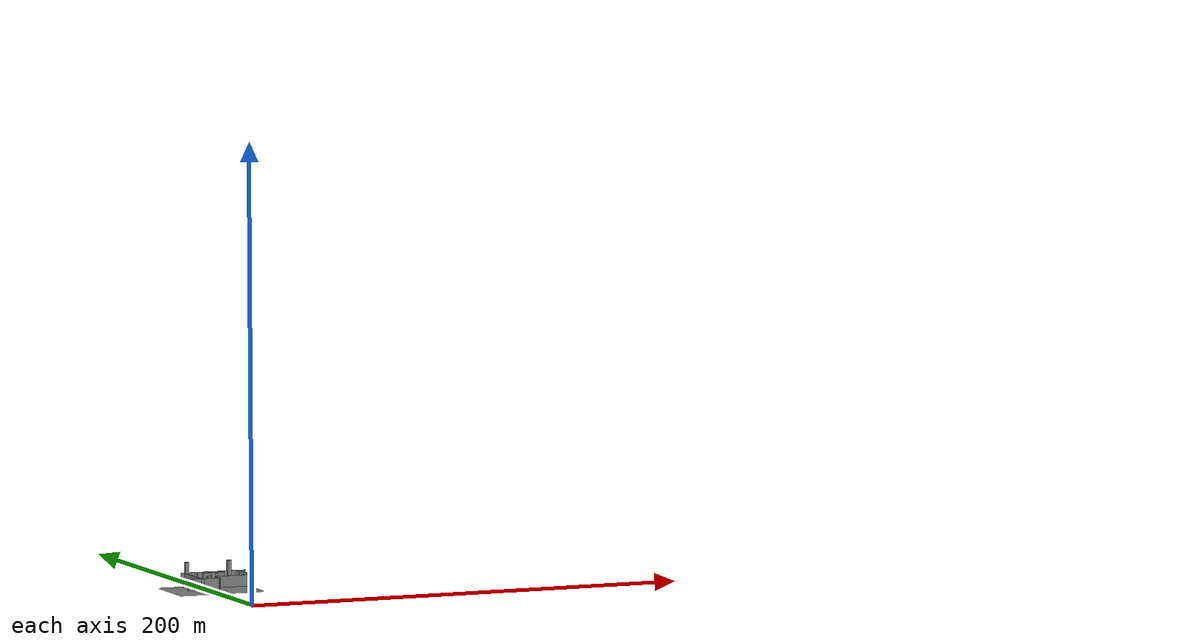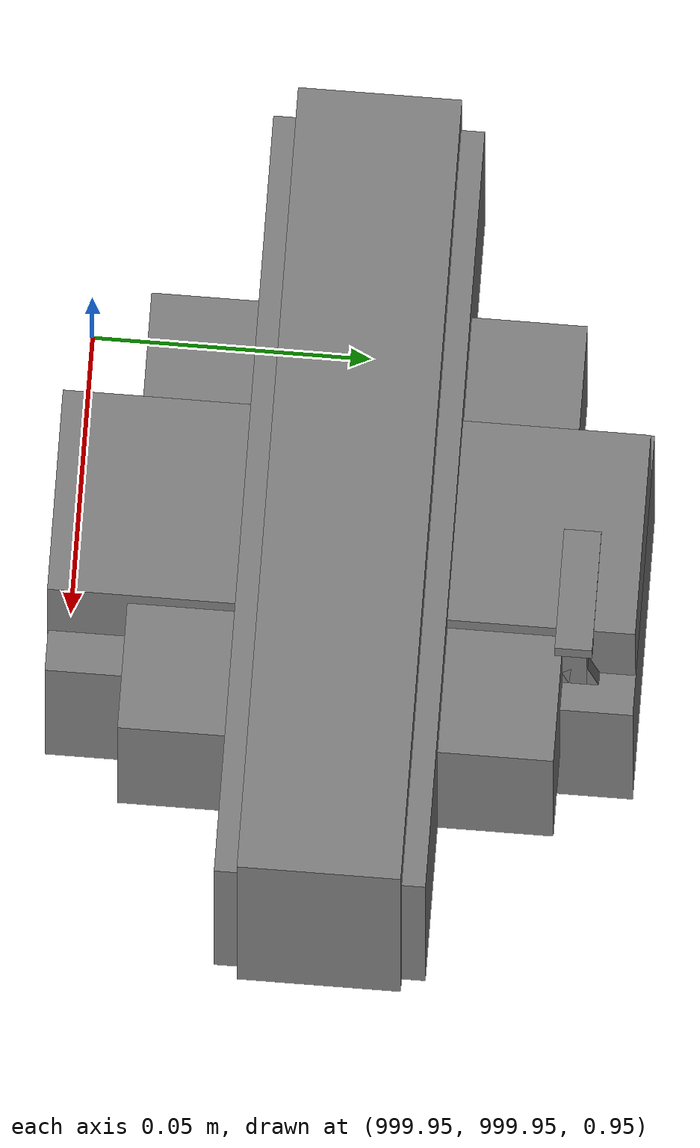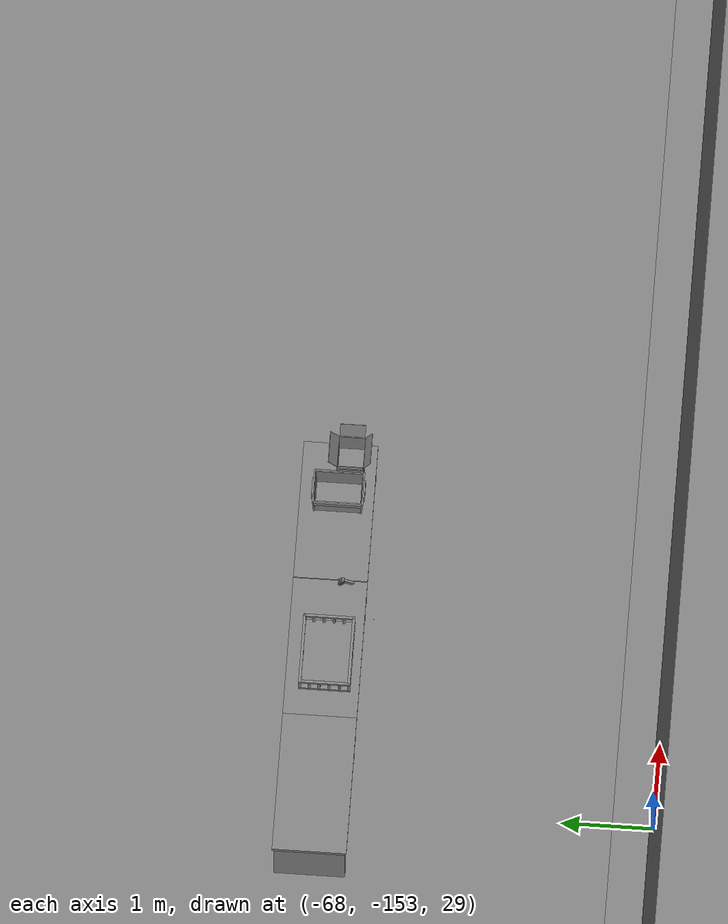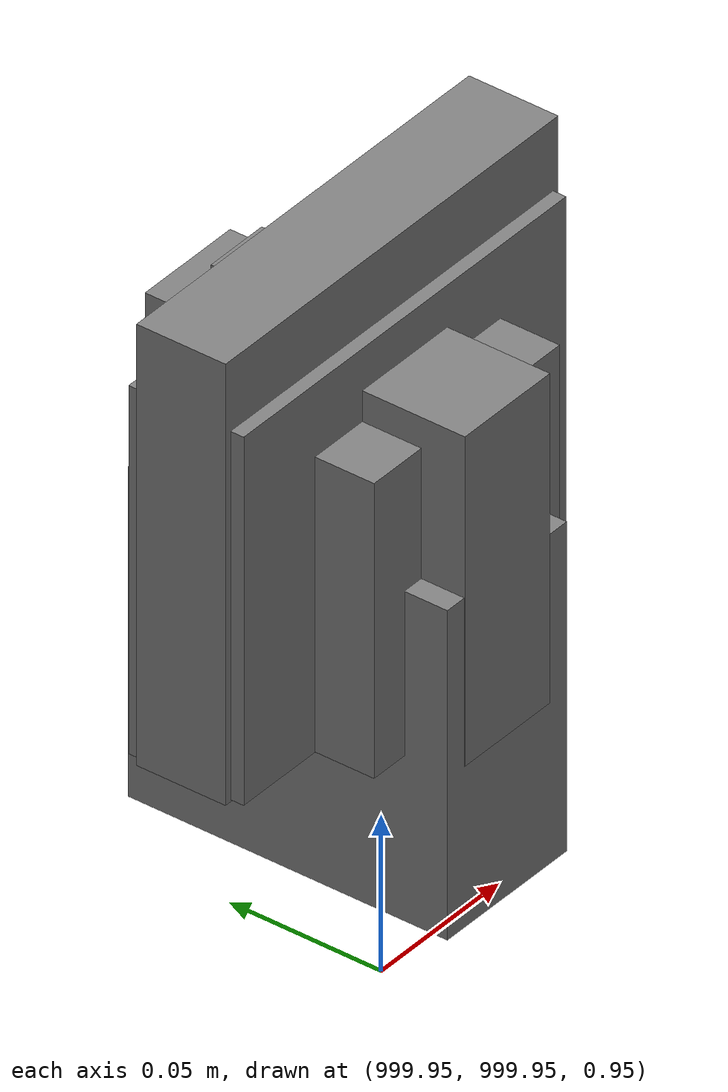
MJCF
<mujoco>
    <option gravity="0.000000000 0.000000000 -9.810000420" timestep="0.0049999999" integrator="implicitfast" density="1.225" viscosity="1.8000001e-05" noslip_iterations="10" iterations="100" sdf_iterations="50">
        <flag multiccd="disable"/>
    </option>
    <size memory="1000M"/>
    <compiler coordinate="local"/>
    <worldbody>
        <light cutoff="30" pos="0 1 1" dir="0 -1 -2"/>
        <light cutoff="30" pos="0 -1 1" dir="0 1 -2"/>
        <body pos="-64.866622925 -149.383972168 30.183746338" euler="89.999984741 89.999946594 0.000000000" name="openloong_gripper_2f85_fix_base_usda_bluebox_01">
            <geom contype="1" conaffinity="1" density="1000" type="box" material="" rgba="0.500000000 0.500000000 0.500000000 1.000000000" solimp="0.899999976 0.949999988 0.001000000" friction="1.000000000 0.005000000 0.000100000" solref="0.020000000 1.000000000" margin="0" condim="3" group="0" pos="0.276580811 0.187225342 0.000068665" quat="0.707106948 0.000077471 0.707106352 0.000077486" size="0.100000001 0.057999998 0.010000000" name="openloong_gripper_2f85_fix_base_usda_geom_51216F08_BA55_46D4_A562_105A5E3BBEA7"/>
            <geom contype="1" conaffinity="1" density="1000" type="box" material="" rgba="0.500000000 0.500000000 0.500000000 1.000000000" solimp="0.899999976 0.949999988 0.001000000" friction="1.000000000 0.005000000 0.000100000" solref="0.020000000 1.000000000" margin="0" condim="3" group="0" pos="0.000000000 0.002883911 0.000000000" quat="0.999999881 0.000000000 0.000000000 0.000000000" size="0.254000008 0.003000000 0.172000006" name="openloong_gripper_2f85_fix_base_usda_geom_85B82E1A_C463_47B2_A435_E45843600695"/>
            <geom contype="1" conaffinity="1" density="1000" type="box" material="" rgba="0.500000000 0.500000000 0.500000000 1.000000000" solimp="0.899999976 0.949999988 0.001000000" friction="1.000000000 0.005000000 0.000100000" solref="0.020000000 1.000000000" margin="0" condim="3" group="0" pos="0.000000000 0.124874115 0.173484802" quat="0.999796331 0.020176515 -0.000000015 0.000000030" size="0.259999990 0.119999997 0.007000000" name="openloong_gripper_2f85_fix_base_usda_geom_E069EB81_5DFD_4642_A377_EE36602C6AD6"/>
            <geom contype="1" conaffinity="1" density="1000" type="box" material="" rgba="0.500000000 0.500000000 0.500000000 1.000000000" solimp="0.899999976 0.949999988 0.001000000" friction="1.000000000 0.005000000 0.000100000" solref="0.020000000 1.000000000" margin="0" condim="3" group="0" pos="0.000000000 0.124874115 -0.173469543" quat="0.999796331 -0.020176545 -0.000000015 0.000000000" size="0.259999990 0.119999997 0.007000000" name="openloong_gripper_2f85_fix_base_usda_geom_26F4EC49_FD09_42BC_9880_5CFB6962A602"/>
            <geom contype="1" conaffinity="1" density="1000" type="box" material="" rgba="0.500000000 0.500000000 0.500000000 1.000000000" solimp="0.899999976 0.949999988 0.001000000" friction="1.000000000 0.005000000 0.000100000" solref="0.020000000 1.000000000" margin="0" condim="3" group="0" pos="0.000000000 0.214008331 0.188980103" quat="0.999912977 0.013176724 0.000000015 0.000000000" size="0.259999990 0.029999999 0.012500000" name="openloong_gripper_2f85_fix_base_usda_geom_CF410CDA_E84D_490C_B455_61259CA35A3C"/>
            <geom contype="1" conaffinity="1" density="1000" type="box" material="" rgba="0.500000000 0.500000000 0.500000000 1.000000000" solimp="0.899999976 0.949999988 0.001000000" friction="1.000000000 0.005000000 0.000100000" solref="0.020000000 1.000000000" margin="0" condim="3" group="0" pos="-0.258361816 0.125289917 0.001876831" quat="0.702796936 -0.020792112 0.710783124 0.020769298" size="0.189999998 0.119999997 0.009000000" name="openloong_gripper_2f85_fix_base_usda_geom_4698C8BA_DC7F_45C3_8DCF_C82DCB45F512"/>
            <geom contype="1" conaffinity="1" density="1000" type="box" material="" rgba="0.500000000 0.500000000 0.500000000 1.000000000" solimp="0.899999976 0.949999988 0.001000000" friction="1.000000000 0.005000000 0.000100000" solref="0.020000000 1.000000000" margin="0" condim="3" group="0" pos="0.000000000 0.214008331 -0.188980103" quat="0.999912977 -0.013176769 0.000000030 0.000000015" size="0.259999990 0.029999999 0.012500000" name="openloong_gripper_2f85_fix_base_usda_geom_815E622C_1D45_493B_9EC7_614647D610C3"/>
            <geom contype="1" conaffinity="1" density="1000" type="box" material="" rgba="0.500000000 0.500000000 0.500000000 1.000000000" solimp="0.899999976 0.949999988 0.001000000" friction="1.000000000 0.005000000 0.000100000" solref="0.020000000 1.000000000" margin="0" condim="3" group="0" pos="-0.276611328 0.187225342 0.000068665" quat="0.707106650 0.000077441 0.707106709 0.000077456" size="0.100000001 0.057999998 0.010000000" name="openloong_gripper_2f85_fix_base_usda_geom_94FB6B80_656E_4D67_9BF2_755E68F60484"/>
            <geom contype="1" conaffinity="1" density="1000" type="box" material="" rgba="0.500000000 0.500000000 0.500000000 1.000000000" solimp="0.899999976 0.949999988 0.001000000" friction="1.000000000 0.005000000 0.000100000" solref="0.020000000 1.000000000" margin="0" condim="3" group="0" pos="0.258331299 0.125289917 0.001876831" quat="0.702851415 0.018856421 0.710823774 -0.019329369" size="0.189999998 0.119999997 0.009000000" name="openloong_gripper_2f85_fix_base_usda_geom_3241B6F3_9035_4C66_8CB1_75227D4A75D5"/>
            <freejoint name="openloong_gripper_2f85_fix_base_usda_bluebox_01_joint"/>
            <site size="0.005000000 0.005000000 0.005000000" rgba="0.500000000 0.500000000 0.500000000 1.000000000" pos="0.000000000 0.000000000 0.000000000" quat="0.999961913 0.008726534 0.000000000 0.000000000" group="0" type="sphere" name="openloong_gripper_2f85_fix_base_usda_bluebox_01site"/>
        </body>
        <body pos="-64.496299744 -149.491867065 30.235729218" euler="0.000000000 0.000000000 89.999946594" name="openloong_gripper_2f85_fix_base_usda_cardboardbox_01">
            <geom contype="1" conaffinity="1" density="1000" type="box" material="" rgba="0.500000000 0.500000000 0.500000000 1.000000000" solimp="0.899999976 0.949999988 0.001000000" friction="1.000000000 0.005000000 0.000100000" solref="0.020000000 1.000000000" margin="0" condim="3" group="0" pos="-0.003166199 -0.004086494 0.005052090" quat="1.000000000 0.000000000 0.000000000 0.000000000" size="0.142499998 0.177500010 0.005000000" name="openloong_gripper_2f85_fix_base_usda_geom_14607704_83D5_4008_A686_1A1EF33B0893"/>
            <geom contype="1" conaffinity="1" density="1000" type="box" material="" rgba="0.500000000 0.500000000 0.500000000 1.000000000" solimp="0.899999976 0.949999988 0.001000000" friction="1.000000000 0.005000000 0.000100000" solref="0.020000000 1.000000000" margin="0" condim="3" group="0" pos="-0.003166199 0.170316696 0.150570869" quat="1.000000000 0.000000000 0.000000000 0.000000000" size="0.142499998 0.005000000 0.149999991" name="openloong_gripper_2f85_fix_base_usda_geom_A58D731C_622F_4F2D_AAD7_96C8DC3AB3EF"/>
            <geom contype="1" conaffinity="1" density="1000" type="box" material="" rgba="0.500000000 0.500000000 0.500000000 1.000000000" solimp="0.899999976 0.949999988 0.001000000" friction="1.000000000 0.005000000 0.000100000" solref="0.020000000 1.000000000" margin="0" condim="3" group="0" pos="-0.147399902 -0.005307198 0.150570869" quat="1.000000000 0.000000000 0.000000000 0.000000000" size="0.005000000 0.177500010 0.149999991" name="openloong_gripper_2f85_fix_base_usda_geom_6505C3E2_6B7D_4AFF_928A_AC0D064AE87B"/>
            <geom contype="1" conaffinity="1" density="1000" type="box" material="" rgba="0.500000000 0.500000000 0.500000000 1.000000000" solimp="0.899999976 0.949999988 0.001000000" friction="1.000000000 0.005000000 0.000100000" solref="0.020000000 1.000000000" margin="0" condim="3" group="0" pos="0.140275955 -0.005307198 0.150570869" quat="1.000000000 0.000000000 0.000000000 0.000000000" size="0.005000000 0.177500010 0.149999991" name="openloong_gripper_2f85_fix_base_usda_geom_00E24713_E30C_4393_90EE_A3ED799B8916"/>
            <geom contype="1" conaffinity="1" density="1000" type="box" material="" rgba="0.500000000 0.500000000 0.500000000 1.000000000" solimp="0.899999976 0.949999988 0.001000000" friction="1.000000000 0.005000000 0.000100000" solref="0.020000000 1.000000000" margin="0" condim="3" group="0" pos="-0.003166199 -0.181550980 0.150570869" quat="1.000000000 0.000000000 0.000000000 0.000000000" size="0.142499998 0.005000000 0.149999991" name="openloong_gripper_2f85_fix_base_usda_geom_5DE605B0_3E88_4881_B848_EB1C5DCAA5E9"/>
            <freejoint name="openloong_gripper_2f85_fix_base_usda_cardboardbox_01_joint"/>
            <site size="0.005000000 0.005000000 0.005000000" rgba="0.500000000 0.500000000 0.500000000 1.000000000" pos="0.000000000 0.000000000 0.000000000" quat="0.999961913 0.008726535 0.000000000 0.000000000" group="0" type="sphere" name="openloong_gripper_2f85_fix_base_usda_site_BEE98024_0B74_4C40_B641_90369895F5E8"/>
            <body pos="0.139160156 -0.004048347 0.301930904" euler="-179.999954224 49.383502960 179.999954224" name="openloong_gripper_2f85_fix_base_usda_A1_006">
                <geom contype="1" conaffinity="1" density="1000" type="box" material="" rgba="0.500000000 0.500000000 0.500000000 1.000000000" solimp="0.899999976 0.949999988 0.001000000" friction="1.000000000 0.005000000 0.000100000" solref="0.020000000 1.000000000" margin="0" condim="3" group="0" pos="-0.071587563 0.000009537 0.001745224" quat="0.999999881 0.000000000 0.000000000 0.000000000" size="0.071249999 0.179999992 0.002500000" name="openloong_gripper_2f85_fix_base_usda_geom_67EC0CF4_3F6A_4F2E_A762_CDA83972C804"/>
                <joint armature="0" stiffness="0.07" damping="0.0099999998" axis="0.000000 1.000000 0.000000" type="hinge" name="openloong_gripper_2f85_fix_base_usda_A1_006"/>
            </body>
            <body pos="-0.145902634 -0.004086494 0.301938057" euler="-180.000000000 -60.000011444 -180.000000000" name="openloong_gripper_2f85_fix_base_usda_A2_006">
                <geom contype="1" conaffinity="1" density="1000" type="box" material="" rgba="0.500000000 0.500000000 0.500000000 1.000000000" solimp="0.899999976 0.949999988 0.001000000" friction="1.000000000 0.005000000 0.000100000" solref="0.020000000 1.000000000" margin="0" condim="3" group="0" pos="0.071268082 0.000009537 0.002717972" quat="0.000002921 0.000000000 -0.000000030 0.999999881" size="0.071249999 0.179999992 0.002500000" name="openloong_gripper_2f85_fix_base_usda_geom_A5EDA745_3648_4563_BA1E_1C558F4DF517"/>
                <joint armature="0" stiffness="0.07" damping="0.0099999998" axis="0.000000 1.000000 0.000000" type="hinge" name="openloong_gripper_2f85_fix_base_usda_A2_006"/>
            </body>
            <body pos="-0.003385544 0.175991058 0.301930904" euler="-125.858116150 -0.000004561 0.000002331" name="openloong_gripper_2f85_fix_base_usda_B2_006">
                <geom contype="1" conaffinity="1" density="1000" type="box" material="" rgba="0.500000000 0.500000000 0.500000000 1.000000000" solimp="0.899999976 0.949999988 0.001000000" friction="1.000000000 0.005000000 0.000100000" solref="0.020000000 1.000000000" margin="0" condim="3" group="0" pos="0.000009537 -0.070939064 -0.002470016" quat="0.999614120 0.027776197 -0.000000015 0.000000030" size="0.137500003 0.064999998 0.005000000" name="openloong_gripper_2f85_fix_base_usda_geom_56602B01_E636_4783_8908_8CC79BEEB743"/>
                <joint armature="0" stiffness="0.07" damping="0.0099999998" axis="1.000000 0.000000 0.000000" type="hinge" name="openloong_gripper_2f85_fix_base_usda_B2_006"/>
            </body>
            <body pos="-0.003385544 -0.184140205 0.301938057" euler="147.805557251 0.000000000 0.000000000" name="openloong_gripper_2f85_fix_base_usda_B1_006">
                <geom contype="1" conaffinity="1" density="1000" type="box" material="" rgba="0.500000000 0.500000000 0.500000000 1.000000000" solimp="0.899999976 0.949999988 0.001000000" friction="1.000000000 0.005000000 0.000100000" solref="0.020000000 1.000000000" margin="0" condim="3" group="0" pos="-0.000028610 0.070202351 -0.002703667" quat="0.999614179 -0.027776167 0.000000000 0.000000000" size="0.137500003 0.064999998 0.005000000" name="openloong_gripper_2f85_fix_base_usda_geom_ABC66468_9BB4_441B_89D0_4D4861DF07AF"/>
                <joint armature="0" stiffness="0.07" damping="0.0099999998" axis="1.000000 0.000000 0.000000" type="hinge" name="openloong_gripper_2f85_fix_base_usda_B1_006"/>
            </body>
        </body>
        <body pos="-65.882858276 -149.481979370 30.229999542" euler="-64.487716675 0.000000000 0.000000000" name="openloong_gripper_2f85_fix_base_usda_Barcode">
            <geom contype="1" conaffinity="1" density="1000" type="box" material="" rgba="0.500000000 0.500000000 0.500000000 1.000000000" solimp="0.899999976 0.949999988 0.001000000" friction="1.000000000 0.005000000 0.000100000" solref="0.020000000 1.000000000" margin="0" condim="3" group="0" pos="0.000000000 0.013038635 0.001419067" quat="0.000000000 0.000000000 0.000000000 1.000000119" size="0.034000002 0.010000000 0.017999999" name="openloong_gripper_2f85_fix_base_usda_geom_0BB36C10_D11D_424E_A1D1_DC976AFC68D9"/>
            <geom contype="1" conaffinity="1" density="1000" type="box" material="" rgba="0.500000000 0.500000000 0.500000000 1.000000000" solimp="0.899999976 0.949999988 0.001000000" friction="1.000000000 0.005000000 0.000100000" solref="0.020000000 1.000000000" margin="0" condim="3" group="0" pos="0.000000000 -0.035301208 -0.007095337" quat="0.000000000 0.000000000 -0.043619365 0.999048233" size="0.028999999 0.010000000 0.020000000" name="openloong_gripper_2f85_fix_base_usda_geom_87B56BD9_8EA7_4185_A33F_D205F4B3A32F"/>
            <geom contype="1" conaffinity="1" density="1000" type="box" material="" rgba="0.500000000 0.500000000 0.500000000 1.000000000" solimp="0.899999976 0.949999988 0.001000000" friction="1.000000000 0.005000000 0.000100000" solref="0.020000000 1.000000000" margin="0" condim="3" group="0" pos="0.000000000 -0.043411255 -0.011749268" quat="0.922262907 0.386563420 0.000000000 0.000000000" size="0.026000001 0.010000000 0.020000000" name="openloong_gripper_2f85_fix_base_usda_geom_3DFE67A2_43F9_4AB9_9A94_B1ACE40AA4E9"/>
            <geom contype="1" conaffinity="1" density="1000" type="box" material="" rgba="0.500000000 0.500000000 0.500000000 1.000000000" solimp="0.899999976 0.949999988 0.001000000" friction="1.000000000 0.005000000 0.000100000" solref="0.020000000 1.000000000" margin="0" condim="3" group="0" pos="0.000000000 -0.016967773 -0.031860352" quat="0.000000000 0.000000000 0.000000000 1.000000119" size="0.008000000 0.010000000 0.013000000" name="openloong_gripper_2f85_fix_base_usda_geom_D2944797_DF13_4CC0_9B48_AAF8F7032B9E"/>
            <geom contype="1" conaffinity="1" density="1000" type="box" material="" rgba="0.500000000 0.500000000 0.500000000 1.000000000" solimp="0.899999976 0.949999988 0.001000000" friction="1.000000000 0.005000000 0.000100000" solref="0.020000000 1.000000000" margin="0" condim="3" group="0" pos="0.000000000 -0.001869202 0.000312805" quat="0.953716993 0.300705761 0.000000000 0.000000000" size="0.032000002 0.010000000 0.018999999" name="openloong_gripper_2f85_fix_base_usda_geom_FA122DFE_FC22_4585_A073_378508F67B1A"/>
            <geom contype="1" conaffinity="1" density="1000" type="box" material="" rgba="0.500000000 0.500000000 0.500000000 1.000000000" solimp="0.899999976 0.949999988 0.001000000" friction="1.000000000 0.005000000 0.000100000" solref="0.020000000 1.000000000" margin="0" condim="3" group="0" pos="0.000000000 -0.019531250 -0.003173828" quat="0.953716993 0.300705761 0.000000000 0.000000000" size="0.030999999 0.010000000 0.020000000" name="openloong_gripper_2f85_fix_base_usda_geom_7BD189EB_B2FD_40A4_A51F_94181A6BC493"/>
            <geom contype="1" conaffinity="1" density="1000" type="box" material="" rgba="0.500000000 0.500000000 0.500000000 1.000000000" solimp="0.899999976 0.949999988 0.001000000" friction="1.000000000 0.005000000 0.000100000" solref="0.020000000 1.000000000" margin="0" condim="3" group="0" pos="0.000000000 -0.035301208 -0.007095337" quat="0.953716993 0.300705761 0.000000000 0.000000000" size="0.028999999 0.010000000 0.020000000" name="openloong_gripper_2f85_fix_base_usda_geom_E7AC5E50_0BD3_4580_AB8D_7549052B884E"/>
            <geom contype="1" conaffinity="1" density="1000" type="box" material="" rgba="0.500000000 0.500000000 0.500000000 1.000000000" solimp="0.899999976 0.949999988 0.001000000" friction="1.000000000 0.005000000 0.000100000" solref="0.020000000 1.000000000" margin="0" condim="3" group="0" pos="0.000000000 -0.042617798 -0.071121216" quat="0.000000000 0.000000000 0.000000000 1.000000119" size="0.013000000 0.021000000 0.059999999" name="openloong_gripper_2f85_fix_base_usda_geom_2655697C_AC6F_4B52_9109_9C6D7D7008DE"/>
            <freejoint name="openloong_gripper_2f85_fix_base_usda_Barcode_joint"/>
            <site size="0.005000000 0.005000000 0.005000000" rgba="0.500000000 0.500000000 0.500000000 1.000000000" pos="0.000000000 0.000000000 0.000000000" quat="1.000000000 0.000000000 0.000000000 0.000000000" group="0" type="sphere" name="openloong_gripper_2f85_fix_base_usda_Barcode_site"/>
        </body>
        <body pos="-66.745018005 -149.392349243 30.184000015" euler="0.000000000 0.000000000 89.999946594" name="[22330985847824]_Basket_01">
            <geom contype="1" conaffinity="1" density="1000" type="box" material="" rgba="0.500000000 0.500000000 0.500000000 1.000000000" solimp="0.899999976 0.949999988 0.001000000" friction="1.000000000 0.005000000 0.000100000" solref="0.020000000 1.000000000" margin="0" condim="3" group="0" pos="-0.052425385 0.389207840 0.089787483" quat="0.707107008 0.000000000 0.000000000 0.707106411" size="0.014249999 0.014249999 0.059999999" name="[22330985847824]_geom_F875CD21_1B33_4923_B8F0_2878E0B29DDE"/>
            <geom contype="1" conaffinity="1" density="1000" type="box" material="" rgba="0.500000000 0.500000000 0.500000000 1.000000000" solimp="0.899999976 0.949999988 0.001000000" friction="1.000000000 0.005000000 0.000100000" solref="0.020000000 1.000000000" margin="0" condim="3" group="0" pos="0.264015198 -0.133043289 0.089787483" quat="0.707107008 0.000000000 0.000000000 0.707106411" size="0.014249999 0.014249999 0.059999999" name="[22330985847824]_geom_9975A143_0528_4168_9160_D5860311B21A"/>
            <geom contype="1" conaffinity="1" density="1000" type="box" material="" rgba="0.500000000 0.500000000 0.500000000 1.000000000" solimp="0.899999976 0.949999988 0.001000000" friction="1.000000000 0.005000000 0.000100000" solref="0.020000000 1.000000000" margin="0" condim="3" group="0" pos="-0.264015198 -0.265548706 0.089793205" quat="0.707107008 0.000000000 0.000000000 0.707106411" size="0.014249999 0.014249999 0.059999999" name="[22330985847824]_geom_D2C9AA40_BCA5_49A6_94EE_453F06F02D3A"/>
            <geom contype="1" conaffinity="1" density="1000" type="box" material="" rgba="0.500000000 0.500000000 0.500000000 1.000000000" solimp="0.899999976 0.949999988 0.001000000" friction="1.000000000 0.005000000 0.000100000" solref="0.020000000 1.000000000" margin="0" condim="3" group="0" pos="-0.160263062 -0.389322281 0.089793205" quat="0.707107008 0.000000000 0.000000000 0.707106411" size="0.014249999 0.014249999 0.059999999" name="[22330985847824]_geom_549D0622_832B_48D3_A098_FC3F5AB9A2E7"/>
            <geom contype="1" conaffinity="1" density="1000" type="box" material="" rgba="0.500000000 0.500000000 0.500000000 1.000000000" solimp="0.899999976 0.949999988 0.001000000" friction="1.000000000 0.005000000 0.000100000" solref="0.020000000 1.000000000" margin="0" condim="3" group="0" pos="0.162265778 -0.389322281 0.089787483" quat="0.707107008 0.000000000 0.000000000 0.707106411" size="0.014249999 0.014249999 0.059999999" name="[22330985847824]_geom_9E14FBDD_5486_458C_ACC5_9038770C1868"/>
            <geom contype="1" conaffinity="1" density="1000" type="box" material="" rgba="0.500000000 0.500000000 0.500000000 1.000000000" solimp="0.899999976 0.949999988 0.001000000" friction="1.000000000 0.005000000 0.000100000" solref="0.020000000 1.000000000" margin="0" condim="3" group="0" pos="0.264015198 0.389207840 0.089787483" quat="0.707107008 0.000000000 0.000000000 0.707106411" size="0.014249999 0.014249999 0.059999999" name="[22330985847824]_geom_3C745535_2655_4E15_85F0_BA21CA72F0B3"/>
            <geom contype="1" conaffinity="1" density="1000" type="box" material="" rgba="0.500000000 0.500000000 0.500000000 1.000000000" solimp="0.899999976 0.949999988 0.001000000" friction="1.000000000 0.005000000 0.000100000" solref="0.020000000 1.000000000" margin="0" condim="3" group="0" pos="-0.264015198 -0.133043289 0.089793205" quat="0.707107008 0.000000000 0.000000000 0.707106411" size="0.014249999 0.014249999 0.059999999" name="[22330985847824]_geom_D955733A_57B0_4ABF_99E5_DE936EC6318A"/>
            <geom contype="1" conaffinity="1" density="1000" type="box" material="" rgba="0.500000000 0.500000000 0.500000000 1.000000000" solimp="0.899999976 0.949999988 0.001000000" friction="1.000000000 0.005000000 0.000100000" solref="0.020000000 1.000000000" margin="0" condim="3" group="0" pos="-0.264026642 0.269256592 0.089793205" quat="0.707107008 0.000000000 0.000000000 0.707106411" size="0.014249999 0.014249999 0.059999999" name="[22330985847824]_geom_669BE3CF_6965_4738_8C0C_6E14D16EF2BD"/>
            <geom contype="1" conaffinity="1" density="1000" type="box" material="" rgba="0.500000000 0.500000000 0.500000000 1.000000000" solimp="0.899999976 0.949999988 0.001000000" friction="1.000000000 0.005000000 0.000100000" solref="0.020000000 1.000000000" margin="0" condim="3" group="0" pos="0.054462433 0.389207840 0.089787483" quat="0.707107008 0.000000000 0.000000000 0.707106411" size="0.014249999 0.014249999 0.059999999" name="[22330985847824]_geom_794AE73D_AEFD_4229_9C6D_89682581EEAC"/>
            <geom contype="1" conaffinity="1" density="1000" type="box" material="" rgba="0.500000000 0.500000000 0.500000000 1.000000000" solimp="0.899999976 0.949999988 0.001000000" friction="1.000000000 0.005000000 0.000100000" solref="0.020000000 1.000000000" margin="0" condim="3" group="0" pos="0.054462433 -0.389322281 0.089787483" quat="0.707107008 0.000000000 0.000000000 0.707106411" size="0.014249999 0.014249999 0.059999999" name="[22330985847824]_geom_28F012A1_243E_4771_8528_8FB19AFEF89D"/>
            <geom contype="1" conaffinity="1" density="1000" type="box" material="" rgba="0.500000000 0.500000000 0.500000000 1.000000000" solimp="0.899999976 0.949999988 0.001000000" friction="1.000000000 0.005000000 0.000100000" solref="0.020000000 1.000000000" margin="0" condim="3" group="0" pos="0.264015198 0.269256592 0.089793205" quat="0.707107008 0.000000000 0.000000000 0.707106411" size="0.014249999 0.014249999 0.059999999" name="[22330985847824]_geom_023EF5B7_E92A_4BC4_8233_D879FA7322F6"/>
            <geom contype="1" conaffinity="1" density="1000" type="box" material="" rgba="0.500000000 0.500000000 0.500000000 1.000000000" solimp="0.899999976 0.949999988 0.001000000" friction="1.000000000 0.005000000 0.000100000" solref="0.020000000 1.000000000" margin="0" condim="3" group="0" pos="0.264015198 -0.389322281 0.089787483" quat="0.707107008 0.000000000 0.000000000 0.707106411" size="0.014249999 0.014249999 0.059999999" name="[22330985847824]_geom_B86D5ADC_3335_46F2_B43E_CFF4B839FE6D"/>
            <geom contype="1" conaffinity="1" density="1000" type="box" material="" rgba="0.500000000 0.500000000 0.500000000 1.000000000" solimp="0.899999976 0.949999988 0.001000000" friction="1.000000000 0.005000000 0.000100000" solref="0.020000000 1.000000000" margin="0" condim="3" group="0" pos="0.000000000 0.000000000 0.015998840" quat="0.707107008 0.000000000 0.000000000 0.707106411" size="0.403499991 0.279000014 0.015750000" name="[22330985847824]_geom_72CCFF3F_99B7_4A93_936E_5C5F28469114"/>
            <geom contype="1" conaffinity="1" density="1000" type="box" material="" rgba="0.500000000 0.500000000 0.500000000 1.000000000" solimp="0.899999976 0.949999988 0.001000000" friction="1.000000000 0.005000000 0.000100000" solref="0.020000000 1.000000000" margin="0" condim="3" group="0" pos="0.000000000 -0.389476776 0.163619041" quat="0.707107008 0.000000000 0.000000000 0.707106411" size="0.015000000 0.277500004 0.015750000" name="[22330985847824]_geom_6109CD86_DBEB_4CBF_A589_7FE8F549AF0F"/>
            <geom contype="1" conaffinity="1" density="1000" type="box" material="" rgba="0.500000000 0.500000000 0.500000000 1.000000000" solimp="0.899999976 0.949999988 0.001000000" friction="1.000000000 0.005000000 0.000100000" solref="0.020000000 1.000000000" margin="0" condim="3" group="0" pos="0.162265778 0.389207840 0.089787483" quat="0.707107008 0.000000000 0.000000000 0.707106411" size="0.014249999 0.014249999 0.059999999" name="[22330985847824]_geom_C18B9AA3_4957_4C83_8B0C_791A66094D32"/>
            <geom contype="1" conaffinity="1" density="1000" type="box" material="" rgba="0.500000000 0.500000000 0.500000000 1.000000000" solimp="0.899999976 0.949999988 0.001000000" friction="1.000000000 0.005000000 0.000100000" solref="0.020000000 1.000000000" margin="0" condim="3" group="0" pos="0.000000000 0.389471054 0.163619041" quat="0.707107008 0.000000000 0.000000000 0.707106411" size="0.015000000 0.277500004 0.015750000" name="[22330985847824]_geom_932CE2B6_6A12_468B_9354_72A1BB95426D"/>
            <geom contype="1" conaffinity="1" density="1000" type="box" material="" rgba="0.500000000 0.500000000 0.500000000 1.000000000" solimp="0.899999976 0.949999988 0.001000000" friction="1.000000000 0.005000000 0.000100000" solref="0.020000000 1.000000000" margin="0" condim="3" group="0" pos="-0.263511658 0.000000000 0.163619041" quat="0.707107008 0.000000000 0.000000000 0.707106411" size="0.403499991 0.015000000 0.015750000" name="[22330985847824]_geom_6043FC80_5FD9_4F57_8ECB_E3531D49F6F7"/>
            <geom contype="1" conaffinity="1" density="1000" type="box" material="" rgba="0.500000000 0.500000000 0.500000000 1.000000000" solimp="0.899999976 0.949999988 0.001000000" friction="1.000000000 0.005000000 0.000100000" solref="0.020000000 1.000000000" margin="0" condim="3" group="0" pos="-0.264015198 0.141334534 0.089793205" quat="0.707107008 0.000000000 0.000000000 0.707106411" size="0.014249999 0.014249999 0.059999999" name="[22330985847824]_geom_73806F21_066A_4393_9814_EA56CA4C84F3"/>
            <geom contype="1" conaffinity="1" density="1000" type="box" material="" rgba="0.500000000 0.500000000 0.500000000 1.000000000" solimp="0.899999976 0.949999988 0.001000000" friction="1.000000000 0.005000000 0.000100000" solref="0.020000000 1.000000000" margin="0" condim="3" group="0" pos="0.264015198 -0.265548706 0.089787483" quat="0.707107008 0.000000000 0.000000000 0.707106411" size="0.014249999 0.014249999 0.059999999" name="[22330985847824]_geom_113FC733_F4E7_45BF_A8FF_9AC74151A247"/>
            <geom contype="1" conaffinity="1" density="1000" type="box" material="" rgba="0.500000000 0.500000000 0.500000000 1.000000000" solimp="0.899999976 0.949999988 0.001000000" friction="1.000000000 0.005000000 0.000100000" solref="0.020000000 1.000000000" margin="0" condim="3" group="0" pos="-0.160263062 0.389207840 0.089787483" quat="0.707107008 0.000000000 0.000000000 0.707106411" size="0.014249999 0.014249999 0.059999999" name="[22330985847824]_geom_94A8BE39_F75A_405B_A6D9_052316A4855D"/>
            <geom contype="1" conaffinity="1" density="1000" type="box" material="" rgba="0.500000000 0.500000000 0.500000000 1.000000000" solimp="0.899999976 0.949999988 0.001000000" friction="1.000000000 0.005000000 0.000100000" solref="0.020000000 1.000000000" margin="0" condim="3" group="0" pos="-0.052425385 -0.389322281 0.089787483" quat="0.707107008 0.000000000 0.000000000 0.707106411" size="0.014249999 0.014249999 0.059999999" name="[22330985847824]_geom_2D6309BB_DC0F_4D5C_8055_D04E950ABB63"/>
            <geom contype="1" conaffinity="1" density="1000" type="box" material="" rgba="0.500000000 0.500000000 0.500000000 1.000000000" solimp="0.899999976 0.949999988 0.001000000" friction="1.000000000 0.005000000 0.000100000" solref="0.020000000 1.000000000" margin="0" condim="3" group="0" pos="-0.264026642 -0.389322281 0.089793205" quat="0.707107008 0.000000000 0.000000000 0.707106411" size="0.014249999 0.014249999 0.059999999" name="[22330985847824]_geom_6987189A_4637_4052_B281_FCE739D4A66B"/>
            <geom contype="1" conaffinity="1" density="1000" type="box" material="" rgba="0.500000000 0.500000000 0.500000000 1.000000000" solimp="0.899999976 0.949999988 0.001000000" friction="1.000000000 0.005000000 0.000100000" solref="0.020000000 1.000000000" margin="0" condim="3" group="0" pos="0.264015198 0.141334534 0.089787483" quat="0.707107008 0.000000000 0.000000000 0.707106411" size="0.014249999 0.014249999 0.059999999" name="[22330985847824]_geom_335BBE5F_5461_44A4_9B1D_8FC264872D0E"/>
            <geom contype="1" conaffinity="1" density="1000" type="box" material="" rgba="0.500000000 0.500000000 0.500000000 1.000000000" solimp="0.899999976 0.949999988 0.001000000" friction="1.000000000 0.005000000 0.000100000" solref="0.020000000 1.000000000" margin="0" condim="3" group="0" pos="-0.264015198 0.389207840 0.089793205" quat="0.707107008 0.000000000 0.000000000 0.707106411" size="0.014249999 0.014249999 0.059999999" name="[22330985847824]_geom_8252ABF2_2721_4770_8184_A04E7E73A17A"/>
            <geom contype="1" conaffinity="1" density="1000" type="box" material="" rgba="0.500000000 0.500000000 0.500000000 1.000000000" solimp="0.899999976 0.949999988 0.001000000" friction="1.000000000 0.005000000 0.000100000" solref="0.020000000 1.000000000" margin="0" condim="3" group="0" pos="0.264015198 0.004480362 0.089787483" quat="0.707107008 0.000000000 0.000000000 0.707106411" size="0.014249999 0.014249999 0.059999999" name="[22330985847824]_geom_FB77240E_AB6E_4C45_8D7D_766D2C8E4DB0"/>
            <geom contype="1" conaffinity="1" density="1000" type="box" material="" rgba="0.500000000 0.500000000 0.500000000 1.000000000" solimp="0.899999976 0.949999988 0.001000000" friction="1.000000000 0.005000000 0.000100000" solref="0.020000000 1.000000000" margin="0" condim="3" group="0" pos="0.263694763 -0.000011444 0.163619041" quat="0.707107008 0.000000000 0.000000000 0.707106411" size="0.403499991 0.015000000 0.015750000" name="[22330985847824]_geom_D064F7E9_1ADB_433B_B64C_6904B3C6B059"/>
            <geom contype="1" conaffinity="1" density="1000" type="box" material="" rgba="0.500000000 0.500000000 0.500000000 1.000000000" solimp="0.899999976 0.949999988 0.001000000" friction="1.000000000 0.005000000 0.000100000" solref="0.020000000 1.000000000" margin="0" condim="3" group="0" pos="-0.264015198 0.004480362 0.089793205" quat="0.707107008 0.000000000 0.000000000 0.707106411" size="0.014249999 0.014249999 0.059999999" name="[22330985847824]_geom_BB0DA94F_1DF8_4CF7_B1BE_84F56ED57221"/>
            <freejoint name="[22330985847824]_joint_EA0F6C12_F610_48DD_9D53_4C01740524AB"/>
        </body>
        <body pos="0.000000000 0.000000000 0.000000000" euler="0.000000000 0.000000000 0.000000000" name="Static Objects_Static Objects">
            <geom contype="1" conaffinity="1" density="1000" type="box" material="" rgba="0.500000000 0.500000000 0.500000000 1.000000000" solimp="0.899999976 0.949999988 0.001000000" friction="1.000000000 0.005000000 0.000100000" solref="0.020000000 1.000000000" margin="0" condim="3" group="0" pos="-67.544113159 -149.365814209 29.727830887" quat="0.500000417 0.499999970 0.499999553 0.499999970" size="0.381000012 0.319999993 0.041000001" name="Static Objects_geom_87193AD5_2D0C_4DE1_BCAF_13EC28F3211C"/>
            <geom contype="1" conaffinity="1" density="1000" type="box" material="" rgba="0.500000000 0.500000000 0.500000000 1.000000000" solimp="0.899999976 0.949999988 0.001000000" friction="1.000000000 0.005000000 0.000100000" solref="0.020000000 1.000000000" margin="0" condim="3" group="0" pos="-68.239501953 -149.365814209 30.086868286" quat="0.500000417 0.499999970 0.499999553 0.499999970" size="0.370999992 0.039500002 0.745000005" name="Static Objects_geom_0F24379E_B9F9_4D1A_A619_F7ABDFF1E979"/>
            <geom contype="1" conaffinity="1" density="1000" type="box" material="" rgba="0.500000000 0.500000000 0.500000000 1.000000000" solimp="0.899999976 0.949999988 0.001000000" friction="1.000000000 0.005000000 0.000100000" solref="0.020000000 1.000000000" margin="0" condim="3" group="0" pos="-68.239501953 -149.365814209 30.147235870" quat="0.500000417 0.499999970 0.499999553 0.499999970" size="0.400000006 0.022000000 0.800000012" name="Static Objects_geom_2DBB2C23_D9F2_4577_9E2B_38ED71E86BAA"/>
            <geom contype="1" conaffinity="1" density="1000" type="box" material="" rgba="0.500000000 0.500000000 0.500000000 1.000000000" solimp="0.899999976 0.949999988 0.001000000" friction="1.000000000 0.005000000 0.000100000" solref="0.020000000 1.000000000" margin="0" condim="3" group="0" pos="-68.934890747 -149.365814209 29.727830887" quat="0.500000417 0.499999970 0.499999553 0.499999970" size="0.381000012 0.319999993 0.041000001" name="Static Objects_geom_A6F1A606_9B9B_4848_840E_6A18AC73B414"/>
            <geom contype="1" conaffinity="1" density="1000" type="box" material="" rgba="0.500000000 0.500000000 0.500000000 1.000000000" solimp="0.899999976 0.949999988 0.001000000" friction="1.000000000 0.005000000 0.000100000" solref="0.020000000 1.000000000" margin="0" condim="3" group="0" pos="-68.239501953 -149.365814209 29.561563492" quat="0.500000417 0.499999970 0.499999553 0.499999970" size="0.020000000 0.022000000 0.660000026" name="Static Objects_geom_19ACA56B_0A57_4654_85CB_ACB0A53B9116"/>
            <geom contype="1" conaffinity="1" density="1000" type="box" material="" rgba="0.500000000 0.500000000 0.500000000 1.000000000" solimp="0.899999976 0.949999988 0.001000000" friction="1.000000000 0.005000000 0.000100000" solref="0.020000000 1.000000000" margin="0" condim="3" group="0" pos="-65.945671082 -149.365814209 29.727830887" quat="0.500000417 0.499999970 0.499999553 0.499999970" size="0.381000012 0.319999993 0.041000001" name="Static Objects_geom_F9341A81_41D0_4CD7_803E_6B68035F17FA"/>
            <geom contype="1" conaffinity="1" density="1000" type="box" material="" rgba="0.500000000 0.500000000 0.500000000 1.000000000" solimp="0.899999976 0.949999988 0.001000000" friction="1.000000000 0.005000000 0.000100000" solref="0.020000000 1.000000000" margin="0" condim="3" group="0" pos="-66.641059875 -149.365814209 30.086868286" quat="0.500000417 0.499999970 0.499999553 0.499999970" size="0.370999992 0.039500002 0.745000005" name="Static Objects_geom_1B33DF0F_5CD3_44A9_934F_0FE7D0D8DB4D"/>
            <geom contype="1" conaffinity="1" density="1000" type="box" material="" rgba="0.500000000 0.500000000 0.500000000 1.000000000" solimp="0.899999976 0.949999988 0.001000000" friction="1.000000000 0.005000000 0.000100000" solref="0.020000000 1.000000000" margin="0" condim="3" group="0" pos="-66.641059875 -149.365814209 30.147235870" quat="0.500000417 0.499999970 0.499999553 0.499999970" size="0.400000006 0.022000000 0.800000012" name="Static Objects_geom_431D02EF_D793_4ED0_87A6_880D43E82544"/>
            <geom contype="1" conaffinity="1" density="1000" type="box" material="" rgba="0.500000000 0.500000000 0.500000000 1.000000000" solimp="0.899999976 0.949999988 0.001000000" friction="1.000000000 0.005000000 0.000100000" solref="0.020000000 1.000000000" margin="0" condim="3" group="0" pos="-67.336448669 -149.365814209 29.727830887" quat="0.500000417 0.499999970 0.499999553 0.499999970" size="0.381000012 0.319999993 0.041000001" name="Static Objects_geom_9156462C_73A4_4B49_A200_FC0AB95BB010"/>
            <geom contype="1" conaffinity="1" density="1000" type="box" material="" rgba="0.500000000 0.500000000 0.500000000 1.000000000" solimp="0.899999976 0.949999988 0.001000000" friction="1.000000000 0.005000000 0.000100000" solref="0.020000000 1.000000000" margin="0" condim="3" group="0" pos="-66.641059875 -149.365814209 29.561563492" quat="0.500000417 0.499999970 0.499999553 0.499999970" size="0.020000000 0.022000000 0.660000026" name="Static Objects_geom_6D4D3852_7D73_4395_8BE8_7A68744A93C1"/>
            <geom contype="1" conaffinity="1" density="1000" type="box" material="" rgba="0.500000000 0.500000000 0.500000000 1.000000000" solimp="0.899999976 0.949999988 0.001000000" friction="1.000000000 0.005000000 0.000100000" solref="0.020000000 1.000000000" margin="0" condim="3" group="0" pos="-64.338577271 -149.365814209 29.727830887" quat="0.500000417 0.499999970 0.499999553 0.499999970" size="0.381000012 0.319999993 0.041000001" name="Static Objects_geom_8DD6DBEB_0039_4071_93FE_0A332C55FE82"/>
            <geom contype="1" conaffinity="1" density="1000" type="box" material="" rgba="0.500000000 0.500000000 0.500000000 1.000000000" solimp="0.899999976 0.949999988 0.001000000" friction="1.000000000 0.005000000 0.000100000" solref="0.020000000 1.000000000" margin="0" condim="3" group="0" pos="-65.033966064 -149.365814209 30.086868286" quat="0.500000417 0.499999970 0.499999553 0.499999970" size="0.370999992 0.039500002 0.745000005" name="Static Objects_geom_88888D2B_84C6_46A1_A557_E159571B7FCB"/>
            <geom contype="1" conaffinity="1" density="1000" type="box" material="" rgba="0.500000000 0.500000000 0.500000000 1.000000000" solimp="0.899999976 0.949999988 0.001000000" friction="1.000000000 0.005000000 0.000100000" solref="0.020000000 1.000000000" margin="0" condim="3" group="0" pos="-65.033966064 -149.365814209 30.147235870" quat="0.500000417 0.499999970 0.499999553 0.499999970" size="0.400000006 0.022000000 0.800000012" name="Static Objects_geom_5EA44A77_C5D8_4568_A115_66BF76D4F219"/>
            <geom contype="1" conaffinity="1" density="1000" type="box" material="" rgba="0.500000000 0.500000000 0.500000000 1.000000000" solimp="0.899999976 0.949999988 0.001000000" friction="1.000000000 0.005000000 0.000100000" solref="0.020000000 1.000000000" margin="0" condim="3" group="0" pos="-65.729354858 -149.365814209 29.727830887" quat="0.500000417 0.499999970 0.499999553 0.499999970" size="0.381000012 0.319999993 0.041000001" name="Static Objects_geom_5899F1F3_6FB4_40DC_978C_E2D7C81CFD7B"/>
            <geom contype="1" conaffinity="1" density="1000" type="box" material="" rgba="0.500000000 0.500000000 0.500000000 1.000000000" solimp="0.899999976 0.949999988 0.001000000" friction="1.000000000 0.005000000 0.000100000" solref="0.020000000 1.000000000" margin="0" condim="3" group="0" pos="-65.033966064 -149.365814209 29.561563492" quat="0.500000417 0.499999970 0.499999553 0.499999970" size="0.020000000 0.022000000 0.660000026" name="Static Objects_geom_926CA8A3_98AE_4AA6_AF78_EB96BC731C88"/>
            <geom contype="1" conaffinity="1" density="1000" type="box" material="" rgba="0.500000000 0.500000000 0.500000000 1.000000000" solimp="0.899999976 0.949999988 0.001000000" friction="1.000000000 0.005000000 0.000100000" solref="0.020000000 1.000000000" margin="0" condim="3" group="0" pos="-61.754566193 -137.853729248 33.906845093" quat="0.707107067 0.000000000 0.000000000 0.707106471" size="0.759999990 0.759999990 4.500000000" name="Static Objects_geom_577AB9B3_7376_400A_A69C_D6FEA2F5F8CE"/>
            <geom contype="1" conaffinity="1" density="1000" type="box" material="" rgba="0.500000000 0.500000000 0.500000000 1.000000000" solimp="0.899999976 0.949999988 0.001000000" friction="1.000000000 0.005000000 0.000100000" solref="0.020000000 1.000000000" margin="0" condim="3" group="0" pos="-57.511135101 -144.927108765 31.707921982" quat="1.000000000 0.000000000 0.000000000 0.000000000" size="0.200000003 8.000000000 2.299999952" name="Static Objects_geom_7BE7A324_91F0_4D6F_90F0_1161C88C11B0"/>
            <geom contype="1" conaffinity="1" density="1000" type="box" material="" rgba="0.500000000 0.500000000 0.500000000 1.000000000" solimp="0.899999976 0.949999988 0.001000000" friction="1.000000000 0.005000000 0.000100000" solref="0.020000000 1.000000000" margin="0" condim="3" group="0" pos="-80.517646790 -157.574050903 31.688196182" quat="0.707107067 0.000000000 0.000000000 0.707106471" size="0.600000024 0.600000024 2.299999952" name="Static Objects_geom_1EADAC71_3E5C_4F34_BCD3_20ADD4DAD4B6"/>
            <geom contype="1" conaffinity="1" density="1000" type="box" material="" rgba="0.500000000 0.500000000 0.500000000 1.000000000" solimp="0.899999976 0.949999988 0.001000000" friction="1.000000000 0.005000000 0.000100000" solref="0.020000000 1.000000000" margin="0" condim="3" group="0" pos="-80.711044312 -147.414932251 31.666158676" quat="1.000000000 0.000000000 0.000000000 0.000000000" size="0.200000003 10.000000000 2.299999952" name="Static Objects_geom_773FD247_5D20_4082_8B52_2CB81BDE6FE2"/>
            <geom contype="1" conaffinity="1" density="1000" type="box" material="" rgba="0.500000000 0.500000000 0.500000000 1.000000000" solimp="0.899999976 0.949999988 0.001000000" friction="1.000000000 0.005000000 0.000100000" solref="0.020000000 1.000000000" margin="0" condim="3" group="0" pos="-57.687217712 -137.434692383 31.688196182" quat="0.707107067 0.000000000 0.000000000 0.707106471" size="0.600000024 0.600000024 2.299999952" name="Static Objects_geom_812E885A_71C6_46A0_94D4_BD76B13128E2"/>
            <geom contype="1" conaffinity="1" density="1000" type="box" material="" rgba="0.500000000 0.500000000 0.500000000 1.000000000" solimp="0.899999976 0.949999988 0.001000000" friction="1.000000000 0.005000000 0.000100000" solref="0.020000000 1.000000000" margin="0" condim="3" group="0" pos="-69.537033081 -140.263229370 31.714921951" quat="0.707107067 0.000000000 0.000000000 0.707106471" size="0.759999990 4.500000000 2.299999952" name="Static Objects_geom_1AB25F6C_DED6_4BF6_87D4_59C1D380835B"/>
            <geom contype="1" conaffinity="1" density="1000" type="box" material="" rgba="0.500000000 0.500000000 0.500000000 1.000000000" solimp="0.899999976 0.949999988 0.001000000" friction="1.000000000 0.005000000 0.000100000" solref="0.020000000 1.000000000" margin="0" condim="3" group="0" pos="-80.073638916 -137.853713989 33.906845093" quat="0.707107067 0.000000000 0.000000000 0.707106471" size="0.759999990 0.759999990 4.500000000" name="Static Objects_geom_06B7BB98_1EF1_40CA_8313_555732A62DD2"/>
            <geom contype="1" conaffinity="1" density="1000" type="box" material="" rgba="0.500000000 0.500000000 0.500000000 1.000000000" solimp="0.899999976 0.949999988 0.001000000" friction="1.000000000 0.005000000 0.000100000" solref="0.020000000 1.000000000" margin="0" condim="3" group="0" pos="-73.406707764 -155.734664917 31.707921982" quat="1.000000000 0.000000000 0.000000000 0.000000000" size="0.200000003 3.000000000 2.299999952" name="Static Objects_geom_753D84D5_0BD3_44F9_A7E0_4514B893C6BF"/>
            <geom contype="1" conaffinity="1" density="1000" type="box" material="" rgba="0.500000000 0.500000000 0.500000000 1.000000000" solimp="0.899999976 0.949999988 0.001000000" friction="1.000000000 0.005000000 0.000100000" solref="0.020000000 1.000000000" margin="0" condim="3" group="0" pos="-68.497543335 -137.448257446 31.707921982" quat="0.707107067 0.000000000 0.000000000 0.707106471" size="0.200000003 14.000000000 2.299999952" name="Static Objects_geom_83CB04DD_CA6B_4BB4_A354_970D2BBFE5A7"/>
            <geom contype="1" conaffinity="1" density="1000" type="cylinder" material="" rgba="0.500000000 0.500000000 0.500000000 1.000000000" solimp="0.899999976 0.949999988 0.001000000" friction="1.000000000 0.005000000 0.000100000" solref="0.020000000 1.000000000" margin="0" condim="3" group="0" pos="-68.868522644 -142.134506226 31.711090088" quat="0.707107067 0.000000000 0.000000000 0.707106471" size="0.509999990 2.299999952 1.000000000" name="Static Objects_geom_0CD3D05D_35BA_4BAE_BF82_18DCC21A91F6"/>
            <geom contype="1" conaffinity="1" density="1000" type="plane" material="" rgba="0.500000000 0.500000000 0.500000000 1.000000000" solimp="0.899999976 0.949999988 0.001000000" friction="1.000000000 0.005000000 0.000100000" solref="0.020000000 1.000000000" margin="0" condim="3" group="0" pos="-72.873703003 -147.131927490 29.409669876" quat="1.000000000 0.000000000 0.000000000 0.000000000" size="18.000000000 14.000000000 1.000000000" name="Static Objects_geom_37F316CE_1128_4506_9086_0AA070B99686"/>
            <geom contype="1" conaffinity="1" density="1000" type="box" material="" rgba="0.500000000 0.500000000 0.500000000 1.000000000" solimp="0.899999976 0.949999988 0.001000000" friction="1.000000000 0.005000000 0.000100000" solref="0.020000000 1.000000000" margin="0" condim="3" group="0" pos="-79.943580627 -157.782272339 31.707921982" quat="0.707107067 0.000000000 0.000000000 0.707106471" size="0.200000003 7.000000000 2.299999952" name="Static Objects_geom_C38704A4_171D_4381_A2DE_76A9DF5899B4"/>
            <geom contype="1" conaffinity="1" density="1000" type="box" material="" rgba="0.500000000 0.500000000 0.500000000 1.000000000" solimp="0.899999976 0.949999988 0.001000000" friction="1.000000000 0.005000000 0.000100000" solref="0.020000000 1.000000000" margin="0" condim="3" group="0" pos="-65.421028137 -152.903442383 31.707921982" quat="0.707107067 0.000000000 0.000000000 0.707106471" size="0.200000003 7.800000191 2.299999952" name="Static Objects_geom_06FE550B_F2AE_4D6C_96DC_EBEDEAF2FA05"/>
            <geom contype="1" conaffinity="1" density="1000" type="box" material="" rgba="0.500000000 0.500000000 0.500000000 1.000000000" solimp="0.899999976 0.949999988 0.001000000" friction="1.000000000 0.005000000 0.000100000" solref="0.020000000 1.000000000" margin="0" condim="3" group="0" pos="-74.776908875 -149.964416504 31.688196182" quat="1.000000000 0.000000000 0.000000000 0.000000000" size="0.600000024 0.409999996 2.299999952" name="Static Objects_geom_A0B82AB4_972F_410F_AD63_9CAD659EBB1E"/>
            <geom contype="1" conaffinity="1" density="1000" type="cylinder" material="" rgba="0.500000000 0.500000000 0.500000000 1.000000000" solimp="0.899999976 0.949999988 0.001000000" friction="1.000000000 0.005000000 0.000100000" solref="0.020000000 1.000000000" margin="0" condim="3" group="0" pos="-60.161884308 -142.134506226 31.711090088" quat="0.707107067 0.000000000 0.000000000 0.707106471" size="0.509999990 2.299999952 1.000000000" name="Static Objects_geom_F3BDE04B_B544_49DA_92E6_C15CA4113695"/>
            <geom contype="1" conaffinity="1" density="1000" type="cylinder" material="" rgba="0.500000000 0.500000000 0.500000000 1.000000000" solimp="0.899999976 0.949999988 0.001000000" friction="1.000000000 0.005000000 0.000100000" solref="0.020000000 1.000000000" margin="0" condim="3" group="0" pos="-75.382453918 -149.963455200 31.711090088" quat="0.707107067 0.000000000 0.000000000 0.707106471" size="0.409999996 2.299999952 1.000000000" name="Static Objects_geom_C7D59C1A_8A80_4B89_873F_3F62333E752C"/>
            <geom contype="1" conaffinity="1" density="1000" type="cylinder" material="" rgba="0.500000000 0.500000000 0.500000000 1.000000000" solimp="0.899999976 0.949999988 0.001000000" friction="1.000000000 0.005000000 0.000100000" solref="0.020000000 1.000000000" margin="0" condim="3" group="0" pos="-74.154960632 -149.963455200 31.711090088" quat="0.707107067 0.000000000 0.000000000 0.707106471" size="0.409999996 2.299999952 1.000000000" name="Static Objects_geom_C1FA73CE_9F97_4C82_98DA_1AA1DE932FD7"/>
            <geom contype="1" conaffinity="1" density="1000" type="cylinder" material="" rgba="0.500000000 0.500000000 0.500000000 1.000000000" solimp="0.899999976 0.949999988 0.001000000" friction="1.000000000 0.005000000 0.000100000" solref="0.020000000 1.000000000" margin="0" condim="3" group="0" pos="-77.566612244 -142.134506226 31.711090088" quat="0.707107067 0.000000000 0.000000000 0.707106471" size="0.509999990 2.299999952 1.000000000" name="Static Objects_geom_C4171226_9B3F_43AB_96E6_B77CD553711B"/>
        </body>
        <body pos="1000.000000000 1000.000000000 1.000000000" euler="0.000000000 0.000000000 180.000000000" name="openloong_gripper_2f85_fix_base_usda_cpu_fan">
            <geom contype="1" conaffinity="1" density="1000" type="box" material="" rgba="0.500000000 0.500000000 0.500000000 1.000000000" solimp="0.899999976 0.949999988 0.001000000" friction="1.000000000 0.005000000 0.000100000" solref="0.020000000 1.000000000" margin="0" condim="3" group="0" pos="0.000000000 0.000000000 0.070034981" quat="0.000000000 0.000000000 0.000000000 1.000000000" size="0.070700005 0.014699999 0.070700005" name="openloong_gripper_2f85_fix_base_usda_geom_8A63D6E7_0054_475B_A697_2DAD48B3F4B9"/>
            <freejoint name="openloong_gripper_2f85_fix_base_usda_cpu_fan_joint"/>
            <site size="0.005000000 0.005000000 0.005000000" rgba="0.500000000 0.500000000 0.500000000 1.000000000" pos="0.000000000 0.000000000 0.000000000" quat="0.999961913 0.008726535 0.000000000 0.000000000" group="0" type="sphere" name="openloong_gripper_2f85_fix_base_usda_cpu_fancsite"/>
        </body>
        <body pos="1000.000000000 1000.000000000 1.000000000" euler="0.000000000 0.000000000 180.000000000" name="openloong_gripper_2f85_fix_base_usda_battery_01">
            <geom contype="1" conaffinity="1" density="1000" type="box" material="" rgba="0.500000000 0.500000000 0.500000000 1.000000000" solimp="0.899999976 0.949999988 0.001000000" friction="1.000000000 0.005000000 0.000100000" solref="0.020000000 1.000000000" margin="0" condim="3" group="0" pos="-0.011123657 -0.041940309 0.101691343" quat="1.000000000 0.000000000 0.000000000 0.000000000" size="0.010800000 0.003375000 0.004725000" name="openloong_gripper_2f85_fix_base_usda_geom_389B169E_182C_49C2_889F_609B82DE7CB8"/>
            <geom contype="1" conaffinity="1" density="1000" type="box" material="" rgba="0.500000000 0.500000000 0.500000000 1.000000000" solimp="0.899999976 0.949999988 0.001000000" friction="1.000000000 0.005000000 0.000100000" solref="0.020000000 1.000000000" margin="0" condim="3" group="0" pos="-0.010876465 -0.044247437 0.047066893" quat="0.998702705 -0.050920475 0.000000000 0.000000000" size="0.009450001 0.002700000 0.024975000" name="openloong_gripper_2f85_fix_base_usda_geom_FA0E19B0_6E47_4F0D_A8F1_B87FAED812EC"/>
            <geom contype="1" conaffinity="1" density="1000" type="box" material="" rgba="0.500000000 0.500000000 0.500000000 1.000000000" solimp="0.899999976 0.949999988 0.001000000" friction="1.000000000 0.005000000 0.000100000" solref="0.020000000 1.000000000" margin="0" condim="3" group="0" pos="-0.001235962 -0.000659180 0.047381196" quat="1.000000000 0.000000000 0.000000000 0.000000000" size="0.039420001 0.039150000 0.047250003" name="openloong_gripper_2f85_fix_base_usda_geom_FD992AE0_92E9_499A_902C_1664B5800022"/>
            <geom contype="1" conaffinity="1" density="1000" type="box" material="" rgba="0.500000000 0.500000000 0.500000000 1.000000000" solimp="0.899999976 0.949999988 0.001000000" friction="1.000000000 0.005000000 0.000100000" solref="0.020000000 1.000000000" margin="0" condim="3" group="0" pos="-0.010876465 -0.039138794 0.009851727" quat="1.000000000 0.000000000 0.000000000 0.000000000" size="0.009450001 0.010800000 0.013500000" name="openloong_gripper_2f85_fix_base_usda_geom_2F8937E6_967F_4E28_BED5_77598569596B"/>
            <geom contype="1" conaffinity="1" density="1000" type="box" material="" rgba="0.500000000 0.500000000 0.500000000 1.000000000" solimp="0.899999976 0.949999988 0.001000000" friction="1.000000000 0.005000000 0.000100000" solref="0.020000000 1.000000000" margin="0" condim="3" group="0" pos="-0.010876465 -0.041528322 0.071508206" quat="1.000000000 0.000000000 0.000000000 0.000000000" size="0.009450001 0.002700000 0.027000001" name="openloong_gripper_2f85_fix_base_usda_geom_7FD2DC2F_87DB_41B3_B154_A6C70B4037BB"/>
            <freejoint name="openloong_gripper_2f85_fix_base_usda_battery_01_joint"/>
            <site size="0.005000000 0.005000000 0.005000000" rgba="0.500000000 0.500000000 0.500000000 1.000000000" pos="0.000000000 0.000000000 0.000000000" quat="0.999961913 0.008726500 0.000000000 0.000000000" group="0" type="sphere" name="openloong_gripper_2f85_fix_base_usda_battery_01site"/>
        </body>
        <body pos="-66.177864075 -149.485183716 31.166957855" euler="30.472354889 66.916831970 42.691787720" mocap="true" name="spotlight3_SpotLight"/>
        <body pos="1000.000000000 1000.000000000 1.000000000" euler="0.000000000 0.000000000 180.000000000" name="openloong_gripper_2f85_fix_base_usda_wifi_box">
            <geom contype="1" conaffinity="1" density="1000" type="box" material="" rgba="0.500000000 0.500000000 0.500000000 1.000000000" solimp="0.899999976 0.949999988 0.001000000" friction="1.000000000 0.005000000 0.000100000" solref="0.020000000 1.000000000" margin="0" condim="3" group="0" pos="0.000000000 0.000000000 0.058978677" quat="0.000000000 0.000000047 0.000000000 1.000000000" size="0.068499997 0.018999999 0.059000000" name="openloong_gripper_2f85_fix_base_usda_geom_EF25867F_75AF_4695_B54D_BE0EC8982A4E"/>
            <freejoint name="openloong_gripper_2f85_fix_base_usda_wifi_box_joint"/>
            <site size="0.005000000 0.005000000 0.005000000" rgba="0.500000000 0.500000000 0.500000000 1.000000000" pos="0.000000000 0.000000000 0.000000000" quat="0.999961913 0.008726500 0.000000000 0.000000000" group="0" type="sphere" name="openloong_gripper_2f85_fix_base_usda_wifi_boxsite"/>
        </body>
        <body pos="1000.000000000 1000.000000000 1.000000000" euler="0.000011953 0.000005123 -179.999984741" name="openloong_gripper_2f85_fix_base_usda_intel_box">
            <geom contype="1" conaffinity="1" density="1000" type="box" material="" rgba="0.500000000 0.500000000 0.500000000 1.000000000" solimp="0.899999976 0.949999988 0.001000000" friction="1.000000000 0.005000000 0.000100000" solref="0.020000000 1.000000000" margin="0" condim="3" group="0" pos="0.000000000 -0.000067139 0.000082284" quat="0.707106709 0.000000225 0.000000253 0.707106650" size="0.052800003 0.025300000 0.052800003" name="openloong_gripper_2f85_fix_base_usda_geom_9C0B46D3_550F_43E8_AC33_CA202AC2A63A"/>
            <freejoint name="openloong_gripper_2f85_fix_base_usda_intel_box_joint"/>
            <site size="0.005000000 0.005000000 0.005000000" rgba="0.500000000 0.500000000 0.500000000 1.000000000" pos="0.000000000 0.000000000 0.000000000" quat="0.999961913 0.008726500 0.000000000 0.000000000" group="0" type="sphere" name="openloong_gripper_2f85_fix_base_usda_intel_boxsite"/>
        </body>
        <body pos="1000.000000000 999.999938965 1.000000000" euler="0.000000000 0.000000000 180.000000000" name="openloong_gripper_2f85_fix_base_usda_intelcore_i5">
            <geom contype="1" conaffinity="1" density="1000" type="box" material="" rgba="0.500000000 0.500000000 0.500000000 1.000000000" solimp="0.899999976 0.949999988 0.001000000" friction="1.000000000 0.005000000 0.000100000" solref="0.020000000 1.000000000" margin="0" condim="3" group="0" pos="0.000000000 0.000000000 0.051722717" quat="0.707106709 0.000000000 0.000000000 -0.707106769" size="0.052800000 0.018080002 0.052800000" name="openloong_gripper_2f85_fix_base_usda_geom_F3796A8F_E734_48E8_8218_9FF71D70D127"/>
            <freejoint name="openloong_gripper_2f85_fix_base_usda_intelcore_i5_joint"/>
            <site size="0.005000000 0.005000000 0.005000000" rgba="0.500000000 0.500000000 0.500000000 1.000000000" pos="0.000000000 0.000000000 0.000000000" quat="0.999961913 0.008726534 0.000000000 0.000000000" group="0" type="sphere" name="openloong_gripper_2f85_fix_base_usda_intelcore_i5site"/>
        </body>
        <body pos="-65.882247925 -149.075729370 31.163566589" euler="-175.532791138 -52.649581909 -84.683975220" mocap="true" name="spotlight2_SpotLight"/>
        <body pos="-66.300781250 -149.559188843 31.170333862" euler="86.587677002 -54.845458984 -35.092731476" mocap="true" name="spotlight4_SpotLight"/>
        <body pos="-66.291030884 -149.869689941 29.018842697" euler="0.000000000 0.000000000 89.999946594" mocap="true" name="openloong_gripper_2f85_fix_base_usda_leftHandMocap"/>
        <body pos="-66.291030884 -149.869689941 29.018842697" euler="0.000000000 0.000000000 89.999946594" mocap="true" name="openloong_gripper_2f85_fix_base_usda_rightHandMocap"/>
        <body pos="-66.291030884 -149.869689941 30.218843460" euler="0.000000000 0.000000000 89.999946594" name="openloong_gripper_2f85_fix_base_usda_base_link">
            <geom contype="1" conaffinity="1" density="1000" type="mesh" material="" rgba="0.783999979 0.783999979 0.783999979 1.000000000" solimp="0.899999976 0.949999988 0.001000000" friction="1.000000000 0.005000000 0.000100000" solref="0.020000000 1.000000000" margin="0" condim="3" group="3" mesh="base_link" pos="0.000000000 0.000000000 0.000000000" quat="1.000000000 0.000000000 0.000000000 0.000000000" size="1.000000000 1.000000000 1.000000000" name="openloong_gripper_2f85_fix_base_usda__geom_7_1497F7FC_465B_40C1_8729_DD55A7830C66"/>
            <site size="0.005000000 0.005000000 0.005000000" rgba="0.500000000 0.500000000 0.500000000 1.000000000" pos="0.000000000 0.000000000 0.000000000" quat="1.000000000 0.000000000 0.000000000 0.000000000" group="0" type="sphere" name="openloong_gripper_2f85_fix_base_usda_imu"/>
            <inertial mass="22.447001" pos="-0.005664100 -0.001336700 0.238289997" diaginertia="0.374352545 0.277180195 0.220617250" quat="0.999247074 0.035235517 -0.015086859 0.006023135"/>
            <body pos="0.000000000 0.000000000 0.299997330" euler="0.000000000 0.000000000 0.000000000" name="openloong_gripper_2f85_fix_base_usda_dummy_body">
                <geom contype="1" conaffinity="1" density="1000" type="sphere" material="" rgba="0.783999979 0.783999979 0.783999979 1.000000000" solimp="0.899999976 0.949999988 0.001000000" friction="1.000000000 0.005000000 0.000100000" solref="0.020000000 1.000000000" margin="0" condim="3" group="3" pos="0.000000000 0.000000000 0.000000000" quat="1.000000000 0.000000000 0.000000000 0.000000000" size="0.010000000 0.000000000 0.000000000" name="openloong_gripper_2f85_fix_base_usda__geom_8_37F9C7F7_A68A_4EED_940B_72E09E0C350A"/>
                <joint armature="0.0099999998" stiffness="0" damping="0.1" axis="0.000000 0.000000 1.000000" type="hinge" name="openloong_gripper_2f85_fix_base_usda_dummy_joint"/>
                <site size="0.010000000 0.005000000 0.005000000" rgba="0.500000000 0.500000000 0.500000000 1.000000000" pos="0.000000000 0.000000000 0.000000000" quat="1.000000000 0.000000000 0.000000000 0.000000000" group="3" type="sphere" name="openloong_gripper_2f85_fix_base_usda_dummy_site"/>
            </body>
            <body pos="0.009002686 0.000000000 0.406400681" euler="0.000000000 0.000000000 0.000000000" name="openloong_gripper_2f85_fix_base_usda_Link_head_yaw">
                <geom contype="1" conaffinity="1" density="1000" type="mesh" material="" rgba="0.783999979 0.783999979 0.783999979 1.000000000" solimp="0.899999976 0.949999988 0.001000000" friction="1.000000000 0.005000000 0.000100000" solref="0.020000000 1.000000000" margin="0" condim="3" group="3" mesh="Link_head_yaw" pos="0.000000000 0.000000000 0.000000000" quat="1.000000000 0.000000000 0.000000000 0.000000000" size="1.000000000 1.000000000 1.000000000" name="openloong_gripper_2f85_fix_base_usda__geom_10_277D029D_9ECE_473D_8753_9D3FD400D4CE"/>
                <inertial mass="0.84249002" pos="0.000000000 -0.002081400 0.044801001" diaginertia="0.000700588 0.000629000 0.000553812" quat="0.706933022 -0.015675601 0.015677100 0.706933022"/>
                <body pos="0.000000000 -0.034599304 0.048500061" euler="0.000000000 0.000000000 0.000000000" name="openloong_gripper_2f85_fix_base_usda_Link_head_pitch">
                    <geom contype="1" conaffinity="1" density="1000" type="mesh" material="" rgba="0.783999979 0.783999979 0.783999979 1.000000000" solimp="0.899999976 0.949999988 0.001000000" friction="1.000000000 0.005000000 0.000100000" solref="0.020000000 1.000000000" margin="0" condim="3" group="3" mesh="Link_head_pitch" pos="0.000000000 0.000000000 0.000000000" quat="1.000000000 0.000000000 0.000000000 0.000000000" size="1.000000000 1.000000000 1.000000000" name="openloong_gripper_2f85_fix_base_usda__geom_12_E321102B_2C99_4409_8FA0_2E32230D934E"/>
                    <inertial mass="1.3943" pos="0.020569000 0.033004001 0.125000000" diaginertia="0.006381400 0.006289940 0.004481460" quat="0.973390222 0.008406822 0.228157058 0.019624906"/>
                    <body pos="0.000000000 0.029998779 0.000000000" euler="0.000000000 0.000000000 0.000000000" name="openloong_gripper_2f85_fix_base_usda_neck_center_body">
                        <site size="0.010000000 0.005000000 0.005000000" rgba="0.500000000 0.500000000 0.500000000 1.000000000" pos="0.000000000 0.000000000 0.000000000" quat="1.000000000 0.000000000 0.000000000 0.000000000" group="3" type="sphere" name="openloong_gripper_2f85_fix_base_usda_neck_center_site"/>
                        <body pos="0.020004272 0.000000000 0.149999619" euler="-0.000002229 39.998176575 -90.000205994" name="openloong_gripper_2f85_fix_base_usda_camera_head">
                            <site size="0.010000000 0.005000000 0.005000000" rgba="0.500000000 0.500000000 0.500000000 1.000000000" pos="0.000000000 0.000000000 0.000000000" quat="1.000000000 0.000000000 0.000000000 0.000000000" group="3" type="sphere" name="openloong_gripper_2f85_fix_base_usda_camera_head_site"/>
                        </body>
                    </body>
                </body>
            </body>
            <body pos="0.003997803 -0.161598206 0.392200470" euler="0.000000000 0.000000000 0.000000000" name="openloong_gripper_2f85_fix_base_usda_Link_arm_r_01">
                <geom contype="1" conaffinity="1" density="1000" type="mesh" material="" rgba="0.783999979 0.783999979 0.783999979 1.000000000" solimp="0.899999976 0.949999988 0.001000000" friction="1.000000000 0.005000000 0.000100000" solref="0.020000000 1.000000000" margin="0" condim="3" group="3" mesh="Link_arm_r_01" pos="0.000000000 0.000000000 0.000000000" quat="1.000000000 0.000000000 0.000000000 0.000000000" size="1.000000000 1.000000000 1.000000000" name="openloong_gripper_2f85_fix_base_usda__geom_14_462BE7FE_EB62_4932_8B7B_49F662943578"/>
                <joint armature="0.0099999998" stiffness="0" damping="1" axis="0.000000 -1.000000 0.000000" limited="true" range="-170.000015259 170.000015259" type="hinge" name="openloong_gripper_2f85_fix_base_usda_J_arm_r_01"/>
                <inertial mass="0.75641" pos="0.004494600 -0.038293999 -0.000001874" diaginertia="0.000842990 0.000803050 0.000587120" quat="-0.000163502 0.707098067 0.000812463 0.707115054"/>
                <body pos="-0.041992188 -0.041000366 0.000000000" euler="0.000000000 0.000000000 0.000000000" name="openloong_gripper_2f85_fix_base_usda_Link_arm_r_02">
                    <geom contype="1" conaffinity="1" density="1000" type="mesh" material="" rgba="0.783999979 0.783999979 0.783999979 1.000000000" solimp="0.899999976 0.949999988 0.001000000" friction="1.000000000 0.005000000 0.000100000" solref="0.020000000 1.000000000" margin="0" condim="3" group="3" mesh="Link_arm_r_02" pos="0.000000000 0.000000000 0.000000000" quat="1.000000000 0.000000000 0.000000000 0.000000000" size="1.000000000 1.000000000 1.000000000" name="openloong_gripper_2f85_fix_base_usda__geom_16_F79B3A63_107D_4245_B6DD_09866A5A7D89"/>
                    <joint armature="0.0099999998" stiffness="0" damping="1" axis="-1.000000 0.000000 0.000000" limited="true" range="-105.000244141 105.000244141" type="hinge" name="openloong_gripper_2f85_fix_base_usda_J_arm_r_02"/>
                    <inertial mass="0.98500001" pos="0.041999999 -0.067430697 0.000000000" diaginertia="0.002262690 0.001730990 0.001154020" quat="0.500000000 0.500000000 -0.500000000 0.500000000"/>
                    <body pos="0.041992188 -0.122596741 0.000000000" euler="0.000000000 0.000000000 0.000000000" name="openloong_gripper_2f85_fix_base_usda_Link_arm_r_03">
                        <geom contype="1" conaffinity="1" density="1000" type="mesh" material="" rgba="0.783999979 0.783999979 0.783999979 1.000000000" solimp="0.899999976 0.949999988 0.001000000" friction="1.000000000 0.005000000 0.000100000" solref="0.020000000 1.000000000" margin="0" condim="3" group="3" mesh="Link_arm_r_03" pos="0.000000000 0.000000000 0.000000000" quat="1.000000000 0.000000000 0.000000000 0.000000000" size="1.000000000 1.000000000 1.000000000" name="openloong_gripper_2f85_fix_base_usda__geom_18_F91747C6_9280_4064_BA8A_92089641B413"/>
                        <joint armature="0.0099999998" stiffness="0" damping="1" axis="0.000000 -1.000000 0.000000" limited="true" range="-170.000015259 170.000015259" type="hinge" name="openloong_gripper_2f85_fix_base_usda_J_arm_r_03"/>
                        <inertial mass="0.95899999" pos="-0.001413580 -0.164663002 0.020757901" diaginertia="0.002101340 0.002064590 0.000754802" quat="0.560480952 0.454391927 -0.443732947 0.531497955"/>
                        <body pos="0.035293579 -0.177406311 0.023998260" euler="0.000000000 0.000000000 0.000000000" name="openloong_gripper_2f85_fix_base_usda_Link_arm_r_04">
                            <geom contype="1" conaffinity="1" density="1000" type="mesh" material="" rgba="0.783999979 0.783999979 0.783999979 1.000000000" solimp="0.899999976 0.949999988 0.001000000" friction="1.000000000 0.005000000 0.000100000" solref="0.020000000 1.000000000" margin="0" condim="3" group="3" mesh="Link_arm_r_04" pos="0.000000000 0.000000000 0.000000000" quat="1.000000000 0.000000000 0.000000000 0.000000000" size="1.000000000 1.000000000 1.000000000" name="openloong_gripper_2f85_fix_base_usda__geom_20_E10ACD26_8670_4B81_BB7B_F4933FC814DC"/>
                            <joint armature="0.0099999998" stiffness="0" damping="1" axis="-1.000000 0.000000 0.000000" limited="true" range="0.000000000 170.000015259" type="hinge" name="openloong_gripper_2f85_fix_base_usda_J_arm_r_04"/>
                            <inertial mass="0.60000002" pos="-0.038727000 -0.060766999 -0.021003000" diaginertia="0.001092610 0.000712422 0.000645102" quat="0.327701002 0.632602990 -0.467366993 0.523443997"/>
                            <body pos="-0.035293579 -0.103492737 -0.023998260" euler="0.000000000 0.000000000 0.000000000" name="openloong_gripper_2f85_fix_base_usda_Link_arm_r_05">
                                <geom contype="1" conaffinity="1" density="1000" type="mesh" material="" rgba="0.783999979 0.783999979 0.783999979 1.000000000" solimp="0.899999976 0.949999988 0.001000000" friction="1.000000000 0.005000000 0.000100000" solref="0.020000000 1.000000000" margin="0" condim="3" group="3" mesh="Link_arm_r_05" pos="0.000000000 0.000000000 0.000000000" quat="1.000000000 0.000000000 0.000000000 0.000000000" size="1.000000000 1.000000000 1.000000000" name="openloong_gripper_2f85_fix_base_usda__geom_22_1DE24A3D_A236_446D_BDF7_44402B45872B"/>
                                <joint armature="0.0099999998" stiffness="0" damping="1" axis="0.000000 -1.000000 0.000000" limited="true" range="-170.000015259 170.000015259" type="hinge" name="openloong_gripper_2f85_fix_base_usda_J_arm_r_05"/>
                                <inertial mass="0.68976003" pos="0.000032712 -0.068658002 -0.000111780" diaginertia="0.002522510 0.002411100 0.000448695" quat="0.707660973 0.706543028 -0.002603360 0.002470550"/>
                                <body pos="-0.026489258 -0.196502686 0.000000000" euler="0.000000000 0.000000000 0.000000000" name="openloong_gripper_2f85_fix_base_usda_Link_arm_r_06">
                                    <geom contype="1" conaffinity="1" density="1000" type="mesh" material="" rgba="0.783999979 0.783999979 0.783999979 1.000000000" solimp="0.899999976 0.949999988 0.001000000" friction="1.000000000 0.005000000 0.000100000" solref="0.020000000 1.000000000" margin="0" condim="3" group="3" mesh="Link_arm_r_06" pos="0.000000000 0.000000000 0.000000000" quat="1.000000000 0.000000000 0.000000000 0.000000000" size="1.000000000 1.000000000 1.000000000" name="openloong_gripper_2f85_fix_base_usda__geom_24_DB7D763F_C9C4_4A4D_BC19_DC8256148724"/>
                                    <joint armature="0.0099999998" stiffness="0" damping="1" axis="1.000000 0.000000 0.000000" limited="true" range="-105.000244141 105.000244141" type="hinge" name="openloong_gripper_2f85_fix_base_usda_J_arm_r_06"/>
                                    <inertial mass="0.28" pos="0.026078001 -0.000000896 0.001663700" diaginertia="0.000156930 0.000145601 0.000104979" quat="0.707080841 0.001851080 0.001883810 0.707127810"/>
                                    <body pos="0.026489258 0.000000000 0.031799316" euler="0.000000000 0.000000000 0.000000000" name="openloong_gripper_2f85_fix_base_usda_Link_arm_r_07">
                                        <geom contype="1" conaffinity="1" density="1000" type="mesh" material="" rgba="0.783999979 0.783999979 0.783999979 1.000000000" solimp="0.899999976 0.949999988 0.001000000" friction="1.000000000 0.005000000 0.000100000" solref="0.020000000 1.000000000" margin="0" condim="3" group="3" mesh="Link_arm_r_07" pos="0.000000000 0.000000000 0.000000000" quat="1.000000000 0.000000000 0.000000000 0.000000000" size="1.000000000 1.000000000 1.000000000" name="openloong_gripper_2f85_fix_base_usda__geom_26_AE371B68_9082_4C69_B866_3A65F7BDCA12"/>
                                        <joint armature="0.0099999998" stiffness="0" damping="1" axis="0.000000 0.000000 1.000000" limited="true" range="-60.000133514 60.000133514" type="hinge" name="openloong_gripper_2f85_fix_base_usda_J_arm_r_07"/>
                                        <inertial mass="0.61353999" pos="-0.007859000 -0.158170000 -0.027736001" diaginertia="0.003037610 0.002570910 0.000729379" quat="0.427542925 0.443532884 -0.553093910 0.560867906"/>
                                        <body pos="0.000000000 0.286994934 -0.270000458" euler="150.000350952 -0.000001649 -0.000000442" name="openloong_gripper_2f85_fix_base_usda_camera_wrist_r">
                                            <site size="0.010000000 0.005000000 0.005000000" rgba="0.500000000 0.500000000 0.500000000 1.000000000" pos="0.000000000 0.000000000 0.000000000" quat="1.000000000 0.000000000 0.000000000 0.000000000" group="3" type="sphere" name="openloong_gripper_2f85_fix_base_usda_camera_wrist_r_site"/>
                                        </body>
                                        <body pos="0.000000000 -0.220008850 -0.033002853" euler="0.000000000 0.000000000 179.999969482" name="openloong_gripper_2f85_fix_base_usda_ee_center_body_r">
                                            <site size="0.010000000 0.005000000 0.005000000" rgba="0.500000000 0.500000000 0.500000000 1.000000000" pos="0.000000000 0.000000000 0.000000000" quat="1.000000000 0.000000000 0.000000000 0.000000000" group="3" type="sphere" name="openloong_gripper_2f85_fix_base_usda_ee_center_site_r"/>
                                        </body>
                                        <body pos="0.000000000 -0.066001892 -0.031000137" euler="89.999984741 0.000000000 180.000000000" name="openloong_gripper_2f85_fix_base_usda_zbr_base_link">
                                            <geom contype="1" conaffinity="1" density="1000" type="mesh" material="" rgba="0.783999979 0.783999979 0.783999979 1.000000000" solimp="0.899999976 0.949999988 0.001000000" friction="1.000000000 0.005000000 0.000100000" solref="0.020000000 1.000000000" margin="0" condim="3" group="3" mesh="base" pos="0.000000000 0.000003815 -0.000007629" quat="1.000000000 0.000000000 0.000000000 0.000000000" size="1.000000238 1.000000238 1.000000238" name="openloong_gripper_2f85_fix_base_usda__geom_30_5588AACF_3900_41B1_8A64_A58A54232F04"/>
                                            <inertial mass="0.77744102" pos="0.000000000 -0.000027039 0.035467502" diaginertia="0.000260285 0.000225381 0.000152708" quat="0.999998808 -0.001528488 0.000000000 0.000000000"/>
                                            <body pos="-0.030609138 0.004745484 0.065696731" euler="-89.999984741 -0.000000000 0.000000000" name="openloong_gripper_2f85_fix_base_usda_r_left_driver">
                                                <geom contype="1" conaffinity="1" density="1000" type="mesh" material="" rgba="0.783999979 0.783999979 0.783999979 1.000000000" solimp="0.899999976 0.949999988 0.001000000" friction="1.000000000 0.005000000 0.000100000" solref="0.020000000 1.000000000" margin="0" condim="3" group="3" mesh="driver" pos="0.030609138 0.054901138 -0.004699708" quat="0.707106829 0.707106709 0.000000000 -0.000000000" size="1.000000238 1.000000238 1.000000238" name="openloong_gripper_2f85_fix_base_usda__geom_32_C44DF98F_59E4_4453_9E7F_D2450078A31E"/>
                                                <joint armature="0.0049999999" stiffness="0" damping="0.1" axis="0.000000 0.000000 1.000000" limited="true" range="0.000000000 51.566200256" type="hinge" name="openloong_gripper_2f85_fix_base_usda_r_left_driver_joint"/>
                                                <inertial mass="0.0089956298" pos="0.000000000 0.017754700 0.001073140" diaginertia="0.000001724 0.000001609 0.000000322" quat="0.681301236 0.732003212 0.000000000 0.000000000"/>
                                                <body pos="-0.031402595 0.004524232 -0.010200503" euler="0.000000000 0.000000000 180.000000000" name="openloong_gripper_2f85_fix_base_usda_r_left_coupler">
                                                    <geom contype="1" conaffinity="1" density="1000" type="mesh" material="" rgba="0.783999979 0.783999979 0.783999979 1.000000000" solimp="0.899999976 0.949999988 0.001000000" friction="1.000000000 0.005000000 0.000100000" solref="0.020000000 1.000000000" margin="0" condim="3" group="3" mesh="coupler" pos="-0.062011734 -0.050354015 0.005500795" quat="0.707106829 -0.707106709 0.000000000 -0.000000000" size="1.000000238 1.000000238 1.000000238" name="openloong_gripper_2f85_fix_base_usda__geom_34_11474898_2947_4EBA_BBC9_B03A66FD6CAF"/>
                                                    <inertial mass="0.0140974" pos="0.000000000 0.003012090 0.023217499" diaginertia="0.000004162 0.000003522 0.000000888" quat="0.705635548 -0.045590367 0.045590367 0.705635548"/>
                                                </body>
                                            </body>
                                            <body pos="-0.012695315 -0.012001040 0.072212234" euler="-89.999984741 -0.000000000 0.000000000" name="openloong_gripper_2f85_fix_base_usda_r_left_spring_link">
                                                <geom contype="1" conaffinity="1" density="1000" type="mesh" material="" rgba="0.783999979 0.783999979 0.783999979 1.000000000" solimp="0.899999976 0.949999988 0.001000000" friction="1.000000000 0.005000000 0.000100000" solref="0.020000000 1.000000000" margin="0" condim="3" group="3" mesh="spring_link" pos="0.012695315 0.061416641 0.012050631" quat="0.707106829 0.707106709 0.000000000 -0.000000000" size="1.000000238 1.000000238 1.000000238" name="openloong_gripper_2f85_fix_base_usda__geom_36_A9C7BFEF_A7F0_46E7_936E_38D6F69A5859"/>
                                                <joint armature="0.001" stiffness="0.050000001" damping="0.00125" axis="0.000000 0.000000 1.000000" limited="true" range="-17.000000000 51.566200256" type="hinge" name="openloong_gripper_2f85_fix_base_usda_r_left_spring_link_joint"/>
                                                <inertial mass="0.0221642" pos="-0.000000009 0.018162400 0.021265799" diaginertia="0.000008969 0.000006717 0.000002639" quat="0.663403213 -0.244737089 0.244737089 0.663403213"/>
                                                <body pos="-0.038208015 -0.042503368 0.002950669" euler="180.000000000 0.000000000 -0.002185660" name="openloong_gripper_2f85_fix_base_usda_r_left_follower">
                                                    <geom contype="1" conaffinity="1" density="1000" type="mesh" material="" rgba="0.783999979 0.783999979 0.783999979 1.000000000" solimp="0.899999976 0.949999988 0.001000000" friction="1.000000000 0.005000000 0.000100000" solref="0.020000000 1.000000000" margin="0" condim="3" group="3" mesh="tongue" pos="0.050918590 -0.103920005 -0.009099962" quat="0.707106829 -0.707106709 0.000000030 0.000000030" size="1.000000238 1.000000238 1.000000238" name="openloong_gripper_2f85_fix_base_usda__geom_40_C1F30158_5426_41E3_9AA3_3FBE0EA4EF51"/>
                                                    <geom contype="1" conaffinity="1" density="1000" type="mesh" material="" rgba="0.783999979 0.783999979 0.783999979 1.000000000" solimp="0.899999976 0.949999988 0.001000000" friction="1.000000000 0.005000000 0.000100000" solref="0.020000000 1.000000000" margin="0" condim="3" group="3" mesh="follower" pos="0.050918590 -0.103920005 -0.009099962" quat="0.707106829 -0.707106709 0.000000030 0.000000030" size="1.000000238 1.000000238 1.000000238" name="openloong_gripper_2f85_fix_base_usda__geom_39_A54E6046_0FF2_4D91_A6F7_02AAA68BAE5D"/>
                                                    <joint armature="0.001" stiffness="0" damping="0.1" axis="0.000000 0.000000 1.000000" limited="true" range="-49.999961853 51.566200256" type="hinge" name="openloong_gripper_2f85_fix_base_usda_r_left_follower"/>
                                                    <inertial mass="0.0125222" pos="0.000000000 -0.011046000 0.012478600" diaginertia="0.000002674 0.000002456 0.000000602" quat="0.986436546 0.164143041 0.000000000 0.000000000"/>
                                                    <body pos="-0.037765510 -0.103912376 -0.009099962" euler="-89.999984741 0.000000000 0.000004829" name="openloong_gripper_2f85_fix_base_usda_r_left_pad">
                                                        <geom contype="1" conaffinity="1" density="1000" type="box" material="" rgba="0.550000012 0.550000012 0.550000012 1.000000000" solimp="0.949999988 0.990000010 0.001000000" friction="0.699999988 0.005000000 0.000100000" solref="0.020000000 1.000000000" margin="0" condim="3" group="3" mass="1e-06" pos="0.043243419 0.000003815 0.119995147" quat="0.999999881 0.000000000 0.000000000 0.000000000" size="0.002000001 0.011000003 0.009375002" name="openloong_gripper_2f85_fix_base_usda_r_left_pad1_5B0C3CCE_C513_4F77_A720_BD0E6D528DB5"/>
                                                        <geom contype="1" conaffinity="1" density="1000" type="box" material="" rgba="0.449999988 0.449999988 0.449999988 1.000000000" solimp="0.949999988 0.990000010 0.001000000" friction="0.600000024 0.005000000 0.000100000" solref="0.020000000 1.000000000" margin="0" condim="3" group="3" mass="1e-06" pos="0.043243419 0.000003815 0.138748199" quat="0.999999881 0.000000000 0.000000000 0.000000000" size="0.002000001 0.011000003 0.009375002" name="openloong_gripper_2f85_fix_base_usda_r_left_pad2_4CC04461_9CA4_48BC_AF57_9F8D5033C48B"/>
                                                    </body>
                                                </body>
                                            </body>
                                            <body pos="0.030593880 -0.004753114 0.065696731" euler="89.999984741 0.000000000 180.000000000" name="openloong_gripper_2f85_fix_base_usda_r_right_driver">
                                                <geom contype="1" conaffinity="1" density="1000" type="mesh" material="" rgba="0.783999979 0.783999979 0.783999979 1.000000000" solimp="0.899999976 0.949999988 0.001000000" friction="1.000000000 0.005000000 0.000100000" solref="0.020000000 1.000000000" margin="0" condim="3" group="3" mesh="driver" pos="0.030593880 0.054901138 -0.004699708" quat="0.707106829 0.707106709 0.000000000 0.000000000" size="1.000000238 1.000000238 1.000000238" name="openloong_gripper_2f85_fix_base_usda__geom_42_783F1140_681E_404E_9634_47FE3B727489"/>
                                                <joint armature="0.0049999999" stiffness="0" damping="0.1" axis="0.000000 0.000000 1.000000" limited="true" range="0.000000000 51.566200256" type="hinge" name="openloong_gripper_2f85_fix_base_usda_r_right_driver_joint"/>
                                                <inertial mass="0.0089956298" pos="0.000000000 0.017754700 0.001073140" diaginertia="0.000001724 0.000001609 0.000000322" quat="0.681301236 0.732003212 0.000000000 0.000000000"/>
                                                <body pos="-0.031417854 0.004531861 -0.010202411" euler="0.000000000 0.000000000 180.000000000" name="openloong_gripper_2f85_fix_base_usda_r_right_coupler">
                                                    <geom contype="1" conaffinity="1" density="1000" type="mesh" material="" rgba="0.783999979 0.783999979 0.783999979 1.000000000" solimp="0.899999976 0.949999988 0.001000000" friction="1.000000000 0.005000000 0.000100000" solref="0.020000000 1.000000000" margin="0" condim="3" group="3" mesh="coupler" pos="-0.062042251 -0.050376903 0.005500795" quat="0.707106829 -0.707106709 0.000000000 0.000000000" size="1.000000238 1.000000238 1.000000238" name="openloong_gripper_2f85_fix_base_usda__geom_44_03D4846F_118B_474E_AEAB_677C2FE2AE1E"/>
                                                    <inertial mass="0.0140974" pos="0.000000000 0.003012090 0.023217499" diaginertia="0.000004162 0.000003522 0.000000888" quat="0.705635548 -0.045590367 0.045590367 0.705635548"/>
                                                </body>
                                            </body>
                                            <body pos="0.012695315 0.011997226 0.072219864" euler="89.999984741 0.000000000 180.000000000" name="openloong_gripper_2f85_fix_base_usda_r_right_spring_link">
                                                <geom contype="1" conaffinity="1" density="1000" type="mesh" material="" rgba="0.783999979 0.783999979 0.783999979 1.000000000" solimp="0.899999976 0.949999988 0.001000000" friction="1.000000000 0.005000000 0.000100000" solref="0.020000000 1.000000000" margin="0" condim="3" group="3" mesh="spring_link" pos="0.012695315 0.061424270 0.012048724" quat="0.707106829 0.707106709 0.000000000 0.000000000" size="1.000000238 1.000000238 1.000000238" name="openloong_gripper_2f85_fix_base_usda__geom_46_F48591D2_D696_44EE_94C4_CCA4C27D0064"/>
                                                <joint armature="0.001" stiffness="0.050000001" damping="0.00125" axis="0.000000 0.000000 1.000000" limited="true" range="-17.000000000 51.566200256" type="hinge" name="openloong_gripper_2f85_fix_base_usda_r_right_spring_link_joint"/>
                                                <inertial mass="0.0221642" pos="-0.000000009 0.018162400 0.021265799" diaginertia="0.000008969 0.000006717 0.000002639" quat="0.663403213 -0.244737089 0.244737089 0.663403213"/>
                                                <body pos="-0.038208015 -0.042495739 0.002950669" euler="180.000000000 0.000000000 0.000000000" name="openloong_gripper_2f85_fix_base_usda_r_right_follower">
                                                    <geom contype="1" conaffinity="1" density="1000" type="mesh" material="" rgba="0.783999979 0.783999979 0.783999979 1.000000000" solimp="0.899999976 0.949999988 0.001000000" friction="1.000000000 0.005000000 0.000100000" solref="0.020000000 1.000000000" margin="0" condim="3" group="3" mesh="follower" pos="0.050888073 -0.103927635 -0.009099962" quat="0.707106829 -0.707106709 0.000000000 0.000000000" size="1.000000238 1.000000238 1.000000238" name="openloong_gripper_2f85_fix_base_usda__geom_50_EDF6DC3A_F826_4E17_A1A2_50C7FF43F645"/>
                                                    <geom contype="1" conaffinity="1" density="1000" type="mesh" material="" rgba="0.783999979 0.783999979 0.783999979 1.000000000" solimp="0.899999976 0.949999988 0.001000000" friction="1.000000000 0.005000000 0.000100000" solref="0.020000000 1.000000000" margin="0" condim="3" group="3" mesh="tongue" pos="0.050888073 -0.103927635 -0.009099962" quat="0.707106829 -0.707106709 0.000000000 0.000000000" size="1.000000238 1.000000238 1.000000238" name="openloong_gripper_2f85_fix_base_usda__geom_49_2E64E849_E0C7_496F_82A1_45A5684F5F2B"/>
                                                    <joint armature="0.001" stiffness="0" damping="0.1" axis="0.000000 0.000000 1.000000" limited="true" range="-49.999961853 51.566200256" type="hinge" name="openloong_gripper_2f85_fix_base_usda_r_right_follower_joint"/>
                                                    <inertial mass="0.0125222" pos="0.000000000 -0.011046000 0.012478600" diaginertia="0.000002674 0.000002456 0.000000602" quat="0.986436546 0.164143041 0.000000000 0.000000000"/>
                                                    <body pos="-0.037811287 -0.103927635 -0.009099962" euler="-89.999984741 0.000000000 0.000000000" name="openloong_gripper_2f85_fix_base_usda_r_right_pad">
                                                        <geom contype="1" conaffinity="1" density="1000" type="box" material="" rgba="0.449999988 0.449999988 0.449999988 1.000000000" solimp="0.949999988 0.990000010 0.001000000" friction="0.600000024 0.005000000 0.000100000" solref="0.020000000 1.000000000" margin="0" condim="3" group="3" mass="1e-06" pos="0.043258678 0.000000000 0.138748199" quat="1.000000000 0.000000000 0.000000000 0.000000000" size="0.002000001 0.011000003 0.009375002" name="openloong_gripper_2f85_fix_base_usda_r_right_pad2_4069B239_D51D_4275_9ABC_F6E96A322668"/>
                                                        <geom contype="1" conaffinity="1" density="1000" type="box" material="" rgba="0.550000012 0.550000012 0.550000012 1.000000000" solimp="0.949999988 0.990000010 0.001000000" friction="0.699999988 0.005000000 0.000100000" solref="0.020000000 1.000000000" margin="0" condim="3" group="3" mass="1e-06" pos="0.043258678 0.000003815 0.120002776" quat="1.000000000 0.000000000 0.000000000 0.000000000" size="0.002000001 0.011000003 0.009375002" name="openloong_gripper_2f85_fix_base_usda_r_right_pad1_53BEA14A_B445_4955_AC0A_89F78B864572"/>
                                                    </body>
                                                </body>
                                            </body>
                                        </body>
                                    </body>
                                </body>
                            </body>
                        </body>
                    </body>
                </body>
            </body>
            <body pos="0.003997803 0.161590576 0.392200470" euler="0.000000000 0.000000000 0.000000000" name="openloong_gripper_2f85_fix_base_usda_Link_arm_l_01">
                <geom contype="1" conaffinity="1" density="1000" type="mesh" material="" rgba="0.783999979 0.783999979 0.783999979 1.000000000" solimp="0.899999976 0.949999988 0.001000000" friction="1.000000000 0.005000000 0.000100000" solref="0.020000000 1.000000000" margin="0" condim="3" group="3" mesh="Link_arm_l_01" pos="0.000000000 0.000000000 0.000000000" quat="1.000000000 0.000000000 0.000000000 0.000000000" size="1.000000000 1.000000000 1.000000000" name="openloong_gripper_2f85_fix_base_usda__geom_52_94FD6F6A_AAF0_46E9_B3F5_92BBAA838207"/>
                <joint armature="0.0099999998" stiffness="0" damping="1" axis="0.000000 1.000000 0.000000" limited="true" range="-170.000015259 170.000015259" type="hinge" name="openloong_gripper_2f85_fix_base_usda_J_arm_l_01"/>
                <inertial mass="0.75640601" pos="-0.004494650 0.038294200 -0.000001874" diaginertia="0.000842986 0.000803053 0.000587115" quat="-0.000812496 0.707115054 0.000163424 0.707098067"/>
                <body pos="0.042007446 0.041000366 0.000000000" euler="0.000000000 0.000000000 0.000000000" name="openloong_gripper_2f85_fix_base_usda_Link_arm_l_02">
                    <geom contype="1" conaffinity="1" density="1000" type="mesh" material="" rgba="0.783999979 0.783999979 0.783999979 1.000000000" solimp="0.899999976 0.949999988 0.001000000" friction="1.000000000 0.005000000 0.000100000" solref="0.020000000 1.000000000" margin="0" condim="3" group="3" mesh="Link_arm_l_02" pos="0.000000000 0.000000000 0.000000000" quat="1.000000000 0.000000000 0.000000000 0.000000000" size="1.000000000 1.000000000 1.000000000" name="openloong_gripper_2f85_fix_base_usda__geom_54_B92AEF7C_9E40_4E0A_9D29_F9A2080291FC"/>
                    <joint armature="0.0099999998" stiffness="0" damping="1" axis="-1.000000 0.000000 0.000000" limited="true" range="-105.000244141 105.000244141" type="hinge" name="openloong_gripper_2f85_fix_base_usda_J_arm_l_02"/>
                    <inertial mass="0.98500001" pos="-0.041999999 0.067430697 0.000000000" diaginertia="0.002262690 0.001730990 0.001154020" quat="0.500000000 0.500000000 -0.500000000 0.500000000"/>
                    <body pos="-0.042007446 0.122596741 0.000000000" euler="0.000000000 0.000000000 0.000000000" name="openloong_gripper_2f85_fix_base_usda_Link_arm_l_03">
                        <geom contype="1" conaffinity="1" density="1000" type="mesh" material="" rgba="0.783999979 0.783999979 0.783999979 1.000000000" solimp="0.899999976 0.949999988 0.001000000" friction="1.000000000 0.005000000 0.000100000" solref="0.020000000 1.000000000" margin="0" condim="3" group="3" mesh="Link_arm_l_03" pos="0.000000000 0.000000000 0.000000000" quat="1.000000000 0.000000000 0.000000000 0.000000000" size="1.000000000 1.000000000 1.000000000" name="openloong_gripper_2f85_fix_base_usda__geom_56_200C8888_E485_4CCC_85DC_D8043BF50911"/>
                        <joint armature="0.0099999998" stiffness="0" damping="1" axis="0.000000 1.000000 0.000000" limited="true" range="-170.000015259 170.000015259" type="hinge" name="openloong_gripper_2f85_fix_base_usda_J_arm_l_03"/>
                        <inertial mass="0.95899999" pos="0.001413580 0.164663002 0.020757901" diaginertia="0.002101340 0.002064590 0.000754802" quat="0.443732947 0.531497955 -0.560480952 0.454391927"/>
                        <body pos="-0.035293579 0.177406311 0.023998260" euler="0.000000000 0.000000000 0.000000000" name="openloong_gripper_2f85_fix_base_usda_Link_arm_l_04">
                            <geom contype="1" conaffinity="1" density="1000" type="mesh" material="" rgba="0.783999979 0.783999979 0.783999979 1.000000000" solimp="0.899999976 0.949999988 0.001000000" friction="1.000000000 0.005000000 0.000100000" solref="0.020000000 1.000000000" margin="0" condim="3" group="3" mesh="Link_arm_l_04" pos="0.000000000 0.000000000 0.000000000" quat="1.000000000 0.000000000 0.000000000 0.000000000" size="1.000000000 1.000000000 1.000000000" name="openloong_gripper_2f85_fix_base_usda__geom_58_54E46F04_4327_4C4D_A6AB_4CE1CA4B1F57"/>
                            <joint armature="0.0099999998" stiffness="0" damping="1" axis="1.000000 0.000000 0.000000" limited="true" range="0.000000000 170.000015259" type="hinge" name="openloong_gripper_2f85_fix_base_usda_J_arm_l_04"/>
                            <inertial mass="0.60000002" pos="0.038727000 0.060767200 -0.021003200" diaginertia="0.001092570 0.000712419 0.000645098" quat="0.467370987 0.523440003 -0.327692002 0.632607996"/>
                            <body pos="0.035293579 0.103500366 -0.023998260" euler="0.000000000 0.000000000 0.000000000" name="openloong_gripper_2f85_fix_base_usda_Link_arm_l_05">
                                <geom contype="1" conaffinity="1" density="1000" type="mesh" material="" rgba="0.783999979 0.783999979 0.783999979 1.000000000" solimp="0.899999976 0.949999988 0.001000000" friction="1.000000000 0.005000000 0.000100000" solref="0.020000000 1.000000000" margin="0" condim="3" group="3" mesh="Link_arm_l_05" pos="0.000000000 0.000000000 0.000000000" quat="1.000000000 0.000000000 0.000000000 0.000000000" size="1.000000000 1.000000000 1.000000000" name="openloong_gripper_2f85_fix_base_usda__geom_60_F244A147_61F7_41E6_890E_46724914439F"/>
                                <joint armature="0.0099999998" stiffness="0" damping="1" axis="0.000000 1.000000 0.000000" limited="true" range="-170.000015259 170.000015259" type="hinge" name="openloong_gripper_2f85_fix_base_usda_J_arm_l_05"/>
                                <inertial mass="0.68976003" pos="-0.000032712 0.068658002 -0.000111780" diaginertia="0.002522510 0.002411100 0.000448695" quat="0.706543028 0.707660973 0.002470550 -0.002603360"/>
                                <body pos="0.026504517 0.196495056 0.000000000" euler="0.000000000 0.000000000 0.000000000" name="openloong_gripper_2f85_fix_base_usda_Link_arm_l_06">
                                    <geom contype="1" conaffinity="1" density="1000" type="mesh" material="" rgba="0.783999979 0.783999979 0.783999979 1.000000000" solimp="0.899999976 0.949999988 0.001000000" friction="1.000000000 0.005000000 0.000100000" solref="0.020000000 1.000000000" margin="0" condim="3" group="3" mesh="Link_arm_l_06" pos="0.000000000 0.000000000 0.000000000" quat="1.000000000 0.000000000 0.000000000 0.000000000" size="1.000000000 1.000000000 1.000000000" name="openloong_gripper_2f85_fix_base_usda__geom_62_D412360C_BAC5_473A_B0E4_09192E2EBAF8"/>
                                    <joint armature="0.0099999998" stiffness="0" damping="1" axis="-1.000000 0.000000 0.000000" limited="true" range="-105.000244141 105.000244141" type="hinge" name="openloong_gripper_2f85_fix_base_usda_J_arm_l_06"/>
                                    <inertial mass="0.28" pos="-0.026077701 0.000000896 0.001663730" diaginertia="0.000156927 0.000145598 0.000104981" quat="0.707080841 -0.001851280 -0.001884020 0.707127810"/>
                                    <body pos="-0.026504517 0.000000000 0.031799316" euler="0.000000000 0.000000000 0.000000000" name="openloong_gripper_2f85_fix_base_usda_Link_arm_l_07">
                                        <geom contype="1" conaffinity="1" density="1000" type="mesh" material="" rgba="0.783999979 0.783999979 0.783999979 1.000000000" solimp="0.899999976 0.949999988 0.001000000" friction="1.000000000 0.005000000 0.000100000" solref="0.020000000 1.000000000" margin="0" condim="3" group="3" mesh="Link_arm_l_07" pos="0.000000000 0.000000000 0.000000000" quat="1.000000000 0.000000000 0.000000000 0.000000000" size="1.000000000 1.000000000 1.000000000" name="openloong_gripper_2f85_fix_base_usda__geom_64_649E5853_85F9_4B76_9720_31DAC1A0E051"/>
                                        <joint armature="0.0099999998" stiffness="0" damping="1" axis="0.000000 0.000000 1.000000" limited="true" range="-60.000133514 60.000133514" type="hinge" name="openloong_gripper_2f85_fix_base_usda_J_arm_l_07"/>
                                        <inertial mass="0.61353999" pos="-0.007787200 0.157049999 -0.027733000" diaginertia="0.003037200 0.002570420 0.000729374" quat="0.443562120 0.427539080 -0.560871124 0.553070128"/>
                                        <body pos="0.000000000 -0.286994934 -0.270000458" euler="-150.000350952 0.000001955 179.976669312" name="openloong_gripper_2f85_fix_base_usda_camera_wrist_l">
                                            <site size="0.010000000 0.005000000 0.005000000" rgba="0.500000000 0.500000000 0.500000000 1.000000000" pos="0.000000000 0.000000000 0.000000000" quat="1.000000000 0.000000000 0.000000000 0.000000000" group="3" type="sphere" name="openloong_gripper_2f85_fix_base_usda_camera_wrist_l_site"/>
                                        </body>
                                        <body pos="0.000000000 0.220008850 -0.033002853" euler="0.000000000 0.000000000 0.000000000" name="openloong_gripper_2f85_fix_base_usda_ee_center_body">
                                            <site size="0.010000000 0.005000000 0.005000000" rgba="0.500000000 0.500000000 0.500000000 1.000000000" pos="0.000000000 0.000000000 0.000000000" quat="1.000000000 0.000000000 0.000000000 0.000000000" group="3" type="sphere" name="openloong_gripper_2f85_fix_base_usda_ee_center_site"/>
                                        </body>
                                        <body pos="0.000000000 0.066009521 -0.031000137" euler="-90.000007629 0.000000000 0.000000000" name="openloong_gripper_2f85_fix_base_usda_zbll_base_link">
                                            <geom contype="1" conaffinity="1" density="1000" type="mesh" material="" rgba="0.783999979 0.783999979 0.783999979 1.000000000" solimp="0.899999976 0.949999988 0.001000000" friction="1.000000000 0.005000000 0.000100000" solref="0.020000000 1.000000000" margin="0" condim="3" group="3" mesh="base" pos="0.000000000 0.000000000 0.000000000" quat="1.000000000 0.000000000 0.000000000 0.000000000" size="1.000000000 1.000000000 1.000000000" name="openloong_gripper_2f85_fix_base_usda__geom_68_33AB218B_2BA1_4D09_B608_F05265DD9EDF"/>
                                            <inertial mass="0.77744102" pos="0.000000000 -0.000027039 0.035467502" diaginertia="0.000260285 0.000225381 0.000152708" quat="0.999998808 -0.001528488 0.000000000 0.000000000"/>
                                            <body pos="-0.030578613 0.004755020 0.065696716" euler="-89.999984741 0.000000000 0.000000000" name="openloong_gripper_2f85_fix_base_usda_l_left_driver">
                                                <geom contype="1" conaffinity="1" density="1000" type="mesh" material="" rgba="0.783999979 0.783999979 0.783999979 1.000000000" solimp="0.899999976 0.949999988 0.001000000" friction="1.000000000 0.005000000 0.000100000" solref="0.020000000 1.000000000" margin="0" condim="3" group="3" mesh="driver" pos="0.030609131 0.054901123 -0.004699707" quat="0.707106829 0.707106709 0.000000000 0.000000000" size="1.000000000 1.000000000 1.000000000" name="openloong_gripper_2f85_fix_base_usda__geom_70_FD18F2CA_BD37_4540_AE4C_79D83E44FD03"/>
                                                <joint armature="0.0049999999" stiffness="0" damping="0.1" axis="0.000000 0.000000 1.000000" limited="true" range="0.000000000 51.566200256" type="hinge" name="openloong_gripper_2f85_fix_base_usda_l_left_driver_joint"/>
                                                <inertial mass="0.0089956298" pos="0.000000000 0.017754700 0.001073140" diaginertia="0.000001724 0.000001609 0.000000322" quat="0.681301236 0.732003212 0.000000000 0.000000000"/>
                                                <body pos="-0.031402588 0.004531860 -0.010200500" euler="0.000000000 0.000000000 180.000000000" name="openloong_gripper_2f85_fix_base_usda_l_left_coupler">
                                                    <geom contype="1" conaffinity="1" density="1000" type="mesh" material="" rgba="0.783999979 0.783999979 0.783999979 1.000000000" solimp="0.899999976 0.949999988 0.001000000" friction="1.000000000 0.005000000 0.000100000" solref="0.020000000 1.000000000" margin="0" condim="3" group="3" mesh="coupler" pos="-0.062042236 -0.050369263 0.005500793" quat="0.707106829 -0.707106709 0.000000000 0.000000000" size="1.000000000 1.000000000 1.000000000" name="openloong_gripper_2f85_fix_base_usda__geom_72_DEEC795F_C42C_43BD_AC3B_A42F9EF047EF"/>
                                                    <inertial mass="0.0140974" pos="0.000000000 0.003012090 0.023217499" diaginertia="0.000004162 0.000003522 0.000000888" quat="0.705635548 -0.045590367 0.045590367 0.705635548"/>
                                                </body>
                                            </body>
                                            <body pos="-0.012680054 -0.011987686 0.072204590" euler="-89.999984741 0.000000000 0.000000000" name="openloong_gripper_2f85_fix_base_usda_l_left_spring_link">
                                                <geom contype="1" conaffinity="1" density="1000" type="mesh" material="" rgba="0.783999979 0.783999979 0.783999979 1.000000000" solimp="0.899999976 0.949999988 0.001000000" friction="1.000000000 0.005000000 0.000100000" solref="0.020000000 1.000000000" margin="0" condim="3" group="3" mesh="spring_link" pos="0.012725830 0.061431885 0.012050629" quat="0.707106829 0.707106709 0.000000000 0.000000000" size="1.000000000 1.000000000 1.000000000" name="openloong_gripper_2f85_fix_base_usda__geom_74_67B6791D_6B4C_44B9_B39E_A0948AF7ECB5"/>
                                                <joint armature="0.001" stiffness="0.050000001" damping="0.00125" axis="0.000000 0.000000 1.000000" limited="true" range="-17.000000000 51.566200256" type="hinge" name="openloong_gripper_2f85_fix_base_usda_l_left_spring_link_joint"/>
                                                <inertial mass="0.0221642" pos="-0.000000009 0.018162400 0.021265799" diaginertia="0.000008969 0.000006717 0.000002639" quat="0.663403213 -0.244737089 0.244737089 0.663403213"/>
                                                <body pos="-0.038192749 -0.042495728 0.002950668" euler="180.000000000 0.000000000 -0.002185660" name="openloong_gripper_2f85_fix_base_usda_l_left_follower">
                                                    <geom contype="1" conaffinity="1" density="1000" type="mesh" material="" rgba="0.783999979 0.783999979 0.783999979 1.000000000" solimp="0.899999976 0.949999988 0.001000000" friction="1.000000000 0.005000000 0.000100000" solref="0.020000000 1.000000000" margin="0" condim="3" group="3" mesh="follower" pos="0.050933838 -0.103919983 -0.009098053" quat="0.707106829 -0.707106650 0.000000000 -0.000000030" size="1.000000000 1.000000000 1.000000000" name="openloong_gripper_2f85_fix_base_usda__geom_77_7AB92702_2DE7_4E47_A999_028D9F424C52"/>
                                                    <geom contype="1" conaffinity="1" density="1000" type="mesh" material="" rgba="0.783999979 0.783999979 0.783999979 1.000000000" solimp="0.899999976 0.949999988 0.001000000" friction="1.000000000 0.005000000 0.000100000" solref="0.020000000 1.000000000" margin="0" condim="3" group="3" mesh="tongue" pos="0.050933838 -0.103919983 -0.009098053" quat="0.707106829 -0.707106650 0.000000000 -0.000000030" size="1.000000000 1.000000000 1.000000000" name="openloong_gripper_2f85_fix_base_usda__geom_78_194A614B_5C7A_46CC_88E6_1BF073D76447"/>
                                                    <joint armature="0.001" stiffness="0" damping="0.1" axis="0.000000 0.000000 1.000000" limited="true" range="-49.999961853 51.566200256" type="hinge" name="openloong_gripper_2f85_fix_base_usda_l_left_follower"/>
                                                    <inertial mass="0.0125222" pos="0.000000000 -0.011046000 0.012478600" diaginertia="0.000002674 0.000002456 0.000000602" quat="0.986436546 0.164143041 0.000000000 0.000000000"/>
                                                    <body pos="-0.037780762 -0.103919983 -0.009098053" euler="-89.999977112 0.000002415 -0.000002415" name="openloong_gripper_2f85_fix_base_usda_l_left_pad">
                                                        <geom contype="1" conaffinity="1" density="1000" type="box" material="" rgba="0.550000012 0.550000012 0.550000012 1.000000000" solimp="0.949999988 0.990000010 0.001000000" friction="0.699999988 0.005000000 0.000100000" solref="0.020000000 1.000000000" margin="0" condim="3" group="3" mass="1e-06" pos="0.043273926 0.000009537 0.119995117" quat="0.999999881 0.000000000 0.000000000 0.000000000" size="0.002000000 0.011000000 0.009375000" name="openloong_gripper_2f85_fix_base_usda_l_left_pad1_364F8A28_5C56_4B1E_8571_AAC4486F1B3E"/>
                                                        <geom contype="1" conaffinity="1" density="1000" type="box" material="" rgba="0.449999988 0.449999988 0.449999988 1.000000000" solimp="0.949999988 0.990000010 0.001000000" friction="0.600000024 0.005000000 0.000100000" solref="0.020000000 1.000000000" margin="0" condim="3" group="3" mass="1e-06" pos="0.043273926 0.000017166 0.138732910" quat="0.999999881 0.000000000 0.000000000 0.000000000" size="0.002000000 0.011000000 0.009375000" name="openloong_gripper_2f85_fix_base_usda_l_left_pad2_38B4C1D8_8B64_4247_9EEA_7BADBFBBEE7B"/>
                                                    </body>
                                                </body>
                                            </body>
                                            <body pos="0.030609131 -0.004739761 0.065689087" euler="89.999984741 0.000000000 180.000000000" name="openloong_gripper_2f85_fix_base_usda_l_right_driver">
                                                <geom contype="1" conaffinity="1" density="1000" type="mesh" material="" rgba="0.783999979 0.783999979 0.783999979 1.000000000" solimp="0.899999976 0.949999988 0.001000000" friction="1.000000000 0.005000000 0.000100000" solref="0.020000000 1.000000000" margin="0" condim="3" group="3" mesh="driver" pos="0.030593872 0.054901123 -0.004697800" quat="0.707106829 0.707106709 0.000000000 0.000000000" size="1.000000000 1.000000000 1.000000000" name="openloong_gripper_2f85_fix_base_usda__geom_80_0E7E12CB_2893_4D79_9A30_E92DAAE827BE"/>
                                                <joint armature="0.0049999999" stiffness="0" damping="0.1" axis="0.000000 0.000000 1.000000" limited="true" range="0.000000000 51.566200256" type="hinge" name="openloong_gripper_2f85_fix_base_usda_l_right_driver_joint"/>
                                                <inertial mass="0.0089956298" pos="0.000000000 0.017754700 0.001073140" diaginertia="0.000001724 0.000001609 0.000000322" quat="0.681301236 0.732003212 0.000000000 0.000000000"/>
                                                <body pos="-0.031433105 0.004531860 -0.010198593" euler="0.000000000 0.000000000 180.000000000" name="openloong_gripper_2f85_fix_base_usda_l_right_coupler">
                                                    <geom contype="1" conaffinity="1" density="1000" type="mesh" material="" rgba="0.783999979 0.783999979 0.783999979 1.000000000" solimp="0.899999976 0.949999988 0.001000000" friction="1.000000000 0.005000000 0.000100000" solref="0.020000000 1.000000000" margin="0" condim="3" group="3" mesh="coupler" pos="-0.062011719 -0.050369263 0.005502701" quat="0.707106829 -0.707106709 0.000000000 0.000000000" size="1.000000000 1.000000000 1.000000000" name="openloong_gripper_2f85_fix_base_usda__geom_82_363C7276_32BD_4D75_9EC6_D2CBBCB43E0A"/>
                                                    <inertial mass="0.0140974" pos="0.000000000 0.003012090 0.023217499" diaginertia="0.000004162 0.000003522 0.000000888" quat="0.705635548 -0.045590367 0.045590367 0.705635548"/>
                                                </body>
                                            </body>
                                            <body pos="0.012710571 0.012010574 0.072204590" euler="89.999984741 0.000000000 180.000000000" name="openloong_gripper_2f85_fix_base_usda_l_right_spring_link">
                                                <geom contype="1" conaffinity="1" density="1000" type="mesh" material="" rgba="0.783999979 0.783999979 0.783999979 1.000000000" solimp="0.899999976 0.949999988 0.001000000" friction="1.000000000 0.005000000 0.000100000" solref="0.020000000 1.000000000" margin="0" condim="3" group="3" mesh="spring_link" pos="0.012695312 0.061416626 0.012052536" quat="0.707106829 0.707106709 0.000000000 0.000000000" size="1.000000000 1.000000000 1.000000000" name="openloong_gripper_2f85_fix_base_usda__geom_84_53E9B4BB_78E8_48E5_A908_287A991893C6"/>
                                                <joint armature="0.001" stiffness="0.050000001" damping="0.00125" axis="0.000000 0.000000 1.000000" limited="true" range="-17.000000000 51.566200256" type="hinge" name="openloong_gripper_2f85_fix_base_usda_l_right_spring_link_joint"/>
                                                <inertial mass="0.0221642" pos="-0.000000009 0.018162400 0.021265799" diaginertia="0.000008969 0.000006717 0.000002639" quat="0.663403213 -0.244737089 0.244737089 0.663403213"/>
                                                <body pos="-0.038208008 -0.042503357 0.002952576" euler="180.000000000 0.000000000 0.000000000" name="openloong_gripper_2f85_fix_base_usda_l_right_follower">
                                                    <geom contype="1" conaffinity="1" density="1000" type="mesh" material="" rgba="0.783999979 0.783999979 0.783999979 1.000000000" solimp="0.899999976 0.949999988 0.001000000" friction="1.000000000 0.005000000 0.000100000" solref="0.020000000 1.000000000" margin="0" condim="3" group="3" mesh="tongue" pos="0.050903320 -0.103919983 -0.009099960" quat="0.707106829 -0.707106709 -0.000000030 -0.000000030" size="1.000000000 1.000000000 1.000000000" name="openloong_gripper_2f85_fix_base_usda__geom_87_282F0807_EC19_4B31_A7CB_C02BE9B4D321"/>
                                                    <geom contype="1" conaffinity="1" density="1000" type="mesh" material="" rgba="0.783999979 0.783999979 0.783999979 1.000000000" solimp="0.899999976 0.949999988 0.001000000" friction="1.000000000 0.005000000 0.000100000" solref="0.020000000 1.000000000" margin="0" condim="3" group="3" mesh="follower" pos="0.050903320 -0.103919983 -0.009099960" quat="0.707106829 -0.707106709 -0.000000030 -0.000000030" size="1.000000000 1.000000000 1.000000000" name="openloong_gripper_2f85_fix_base_usda__geom_88_D4A5328D_4DB2_4F7B_8B9F_C9FBC5A98A68"/>
                                                    <joint armature="0.001" stiffness="0" damping="0.1" axis="0.000000 0.000000 1.000000" limited="true" range="-49.999961853 51.566200256" type="hinge" name="openloong_gripper_2f85_fix_base_usda_l_right_follower_joint"/>
                                                    <inertial mass="0.0125222" pos="0.000000000 -0.011046000 0.012478600" diaginertia="0.000002674 0.000002456 0.000000602" quat="0.986436546 0.164143041 0.000000000 0.000000000"/>
                                                    <body pos="-0.037796021 -0.103912354 -0.009099960" euler="-89.999984741 -0.000000000 -0.000004830" name="openloong_gripper_2f85_fix_base_usda_l_right_pad">
                                                        <geom contype="1" conaffinity="1" density="1000" type="box" material="" rgba="0.550000012 0.550000012 0.550000012 1.000000000" solimp="0.949999988 0.990000010 0.001000000" friction="0.699999988 0.005000000 0.000100000" solref="0.020000000 1.000000000" margin="0" condim="3" group="3" mass="1e-06" pos="0.043258667 0.000000000 0.119995117" quat="1.000000000 0.000000000 0.000000000 0.000000000" size="0.002000000 0.011000000 0.009375000" name="openloong_gripper_2f85_fix_base_usda_l_right_pad1_AA2895AD_AE24_4694_86C2_7EAD2979E961"/>
                                                        <geom contype="1" conaffinity="1" density="1000" type="box" material="" rgba="0.449999988 0.449999988 0.449999988 1.000000000" solimp="0.949999988 0.990000010 0.001000000" friction="0.600000024 0.005000000 0.000100000" solref="0.020000000 1.000000000" margin="0" condim="3" group="3" mass="1e-06" pos="0.043258667 0.000000000 0.138748169" quat="1.000000000 0.000000000 0.000000000 0.000000000" size="0.002000000 0.011000000 0.009375000" name="openloong_gripper_2f85_fix_base_usda_l_right_pad2_BAA6654F_57AE_4993_A0AF_E4AEAB198830"/>
                                                    </body>
                                                </body>
                                            </body>
                                        </body>
                                    </body>
                                </body>
                            </body>
                        </body>
                    </body>
                </body>
            </body>
            <body pos="0.000000000 -0.065246582 0.000000000" euler="0.000000000 0.000000000 0.000000000" name="openloong_gripper_2f85_fix_base_usda_Link_waist_pitch">
                <geom contype="1" conaffinity="1" density="1000" type="mesh" material="" rgba="0.783999979 0.783999979 0.783999979 1.000000000" solimp="0.899999976 0.949999988 0.001000000" friction="1.000000000 0.005000000 0.000100000" solref="0.020000000 1.000000000" margin="0" condim="3" group="3" mesh="Link_waist_pitch" pos="0.000000000 0.000000000 0.000000000" quat="1.000000000 0.000000000 0.000000000 0.000000000" size="1.000000000 1.000000000 1.000000000" name="openloong_gripper_2f85_fix_base_usda__geom_90_F42FBC55_36B5_4277_AE51_2A5D0C0E8CA8"/>
                <inertial mass="2.6963999" pos="-0.000734960 0.049924999 -0.000029695" diaginertia="0.006190620 0.005201250 0.004737120" quat="0.524125040 0.474713057 -0.522095084 0.476820052"/>
                <body pos="-0.063995361 0.065498352 0.000000000" euler="0.000000000 0.000000000 0.000000000" name="openloong_gripper_2f85_fix_base_usda_Link_waist_roll">
                    <geom contype="1" conaffinity="1" density="1000" type="mesh" material="" rgba="0.783999979 0.783999979 0.783999979 1.000000000" solimp="0.899999976 0.949999988 0.001000000" friction="1.000000000 0.005000000 0.000100000" solref="0.020000000 1.000000000" margin="0" condim="3" group="3" mesh="Link_waist_roll" pos="0.000000000 0.000000000 0.000000000" quat="1.000000000 0.000000000 0.000000000 0.000000000" size="1.000000000 1.000000000 1.000000000" name="openloong_gripper_2f85_fix_base_usda__geom_92_2C705115_A7E0_4E52_A5EC_1AAC37F487D6"/>
                    <inertial mass="2.9806001" pos="-0.003742400 -0.001000000 -0.016856000" diaginertia="0.018825000 0.017314700 0.005873970" quat="0.576995134 0.408750087 0.408750087 0.576995134"/>
                    <body pos="0.067520142 0.000000000 -0.097999573" euler="0.000000000 0.000000000 0.000000000" name="openloong_gripper_2f85_fix_base_usda_Link_waist_yaw">
                        <geom contype="1" conaffinity="1" density="1000" type="mesh" material="" rgba="0.783999979 0.783999979 0.783999979 1.000000000" solimp="0.899999976 0.949999988 0.001000000" friction="1.000000000 0.005000000 0.000100000" solref="0.020000000 1.000000000" margin="0" condim="3" group="3" mesh="Link_waist_yaw" pos="0.000000000 0.000000000 0.000000000" quat="1.000000000 0.000000000 0.000000000 0.000000000" size="1.000000000 1.000000000 1.000000000" name="openloong_gripper_2f85_fix_base_usda__geom_94_114F156C_5134_41E3_A7A3_223EFE1F90FF"/>
                        <inertial mass="7.3587999" pos="-0.096171997 -0.001000000 -0.057836000" diaginertia="0.109522998 0.089752100 0.032765999" quat="0.571972013 0.571972013 -0.415749997 0.415749997"/>
                        <body pos="-0.087493896 -0.120002747 -0.069000244" euler="0.000000000 0.000000000 0.000000000" name="openloong_gripper_2f85_fix_base_usda_Link_hip_r_roll">
                            <geom contype="1" conaffinity="1" density="1000" type="mesh" material="" rgba="0.783999979 0.783999979 0.783999979 1.000000000" solimp="0.899999976 0.949999988 0.001000000" friction="1.000000000 0.005000000 0.000100000" solref="0.020000000 1.000000000" margin="0" condim="3" group="3" mesh="Link_hip_r_roll" pos="0.000000000 0.000000000 0.000000000" quat="1.000000000 0.000000000 0.000000000 0.000000000" size="1.000000000 1.000000000 1.000000000" name="openloong_gripper_2f85_fix_base_usda__geom_96_6CC33EBC_BE73_4259_9E56_C170ED47B170"/>
                            <inertial mass="2.4333999" pos="0.075724997 -0.001061600 0.016590999" diaginertia="0.004506770 0.003996270 0.003606060" quat="0.357336968 0.610613942 0.606069922 0.363510966"/>
                            <body pos="0.082229614 -0.000999451 -0.009998322" euler="0.000000000 0.000000000 0.000000000" name="openloong_gripper_2f85_fix_base_usda_Link_hip_r_yaw">
                                <geom contype="1" conaffinity="1" density="1000" type="mesh" material="" rgba="0.783999979 0.783999979 0.783999979 1.000000000" solimp="0.899999976 0.949999988 0.001000000" friction="1.000000000 0.005000000 0.000100000" solref="0.020000000 1.000000000" margin="0" condim="3" group="3" mesh="Link_hip_r_yaw" pos="0.000000000 0.000000000 0.000000000" quat="1.000000000 0.000000000 0.000000000 0.000000000" size="1.000000000 1.000000000 1.000000000" name="openloong_gripper_2f85_fix_base_usda__geom_98_264CC32D_42C2_429C_B87A_8636B8FE5FC7"/>
                                <inertial mass="3.4303" pos="-0.000000031 -0.007135600 -0.100630000" diaginertia="0.008090100 0.007736500 0.006631600" quat="0.706536055 0.028403703 -0.028403703 0.706536055"/>
                                <body pos="0.000000000 0.036750793 -0.105501175" euler="0.000000000 0.000000000 0.000000000" name="openloong_gripper_2f85_fix_base_usda_Link_hip_r_pitch">
                                    <geom contype="1" conaffinity="1" density="1000" type="mesh" material="" rgba="0.783999979 0.783999979 0.783999979 1.000000000" solimp="0.899999976 0.949999988 0.001000000" friction="1.000000000 0.005000000 0.000100000" solref="0.020000000 1.000000000" margin="0" condim="3" group="3" mesh="Link_hip_r_pitch" pos="0.000000000 0.000000000 0.000000000" quat="1.000000000 0.000000000 0.000000000 0.000000000" size="1.000000000 1.000000000 1.000000000" name="openloong_gripper_2f85_fix_base_usda__geom_100_536DDCE4_F250_4B84_8318_FAE666B49011"/>
                                    <inertial mass="5.2378001" pos="0.001085600 -0.054970000 -0.145349994" diaginertia="0.043490201 0.037812300 0.015138500" quat="0.999495864 -0.015916798 0.013696698 0.023812896"/>
                                    <body pos="0.000000000 -0.011253357 -0.400001526" euler="0.000000000 0.000000000 0.000000000" name="openloong_gripper_2f85_fix_base_usda_Link_knee_r_pitch">
                                        <geom contype="1" conaffinity="1" density="1000" type="mesh" material="" rgba="0.783999979 0.783999979 0.783999979 1.000000000" solimp="0.899999976 0.949999988 0.001000000" friction="1.000000000 0.005000000 0.000100000" solref="0.020000000 1.000000000" margin="0" condim="3" group="3" mesh="Link_knee_r_pitch" pos="0.000000000 0.000000000 0.000000000" quat="1.000000000 0.000000000 0.000000000 0.000000000" size="1.000000000 1.000000000 1.000000000" name="openloong_gripper_2f85_fix_base_usda__geom_102_5656E238_9798_4A4E_A404_C9085CA2380A"/>
                                        <inertial mass="2.9775" pos="-0.009642500 0.000002934 -0.136010006" diaginertia="0.024215899 0.023851801 0.002284610" quat="0.782037616 -0.003061678 0.016178992 0.623013675"/>
                                        <body pos="0.000000000 0.000000000 -0.386999130" euler="0.000000000 0.000000000 0.000000000" name="openloong_gripper_2f85_fix_base_usda_Link_ankle_r_pitch">
                                            <geom contype="1" conaffinity="1" density="1000" type="mesh" material="" rgba="0.783999979 0.783999979 0.783999979 1.000000000" solimp="0.899999976 0.949999988 0.001000000" friction="1.000000000 0.005000000 0.000100000" solref="0.020000000 1.000000000" margin="0" condim="3" group="3" mesh="Link_ankle_r_pitch" pos="0.000000000 0.000000000 0.000000000" quat="1.000000000 0.000000000 0.000000000 0.000000000" size="1.000000000 1.000000000 1.000000000" name="openloong_gripper_2f85_fix_base_usda__geom_104_32FD6EB9_173F_42C2_9F76_8AA0CFB93146"/>
                                            <inertial mass="0.10145" pos="-0.000000000 -0.000000127 -0.000000025" diaginertia="0.000027175 0.000026565 0.000006112" quat="0.707106829 0.707106829 0.000000000 0.000000000"/>
                                            <body pos="0.000000000 0.000000000 0.000000000" euler="0.000000000 0.000000000 0.000000000" name="openloong_gripper_2f85_fix_base_usda_Link_ankle_r_roll">
                                                <geom contype="1" conaffinity="1" density="1000" type="box" material="" rgba="1.000000000 0.000000000 0.000000000 0.000000000" solimp="0.899999976 0.949999988 0.001000000" friction="1.000000000 0.005000000 0.000100000" solref="0.020000000 1.000000000" margin="0" condim="3" group="3" pos="0.047515869 0.000083923 -0.026544571" quat="1.000000000 0.000000000 0.000000000 0.000000000" size="0.122500002 0.039999999 0.043499999" name="openloong_gripper_2f85_fix_base_usda__geom_106_5A9C2FCE_082F_478C_979A_86DCF7067CAA"/>
                                                <site size="0.123000003 0.041000001 0.044000000" rgba="0.000000000 1.000000000 0.000000000 0.000000000" pos="0.047504615 0.000082667 -0.026545310" quat="1.000000000 0.000000000 0.000000000 0.000000000" group="3" type="box" name="openloong_gripper_2f85_fix_base_usda_rf-tc"/>
                                                <inertial mass="0.75229001" pos="0.041078001 -0.000000089 -0.043908998" diaginertia="0.003659370 0.003646500 0.000416828" quat="0.000000000 0.677034914 0.000000000 0.735950947"/>
                                            </body>
                                        </body>
                                    </body>
                                </body>
                            </body>
                        </body>
                        <body pos="-0.087493896 0.120002747 -0.069000244" euler="0.000000000 0.000000000 0.000000000" name="openloong_gripper_2f85_fix_base_usda_Link_hip_l_roll">
                            <geom contype="1" conaffinity="1" density="1000" type="mesh" material="" rgba="0.783999979 0.783999979 0.783999979 1.000000000" solimp="0.899999976 0.949999988 0.001000000" friction="1.000000000 0.005000000 0.000100000" solref="0.020000000 1.000000000" margin="0" condim="3" group="3" mesh="Link_hip_l_roll" pos="0.000000000 0.000000000 0.000000000" quat="1.000000000 0.000000000 0.000000000 0.000000000" size="1.000000000 1.000000000 1.000000000" name="openloong_gripper_2f85_fix_base_usda__geom_108_E3E10506_A874_4B0D_B3BB_6B5359FA6070"/>
                            <inertial mass="2.4333999" pos="0.075724997 -0.000938430 0.016590999" diaginertia="0.004257030 0.003974770 0.003377790" quat="0.411751240 0.573205352 0.583885372 0.401216239"/>
                            <body pos="0.082229614 -0.000999451 -0.009998322" euler="0.000000000 0.000000000 0.000000000" name="openloong_gripper_2f85_fix_base_usda_Link_hip_l_yaw">
                                <geom contype="1" conaffinity="1" density="1000" type="mesh" material="" rgba="0.783999979 0.783999979 0.783999979 1.000000000" solimp="0.899999976 0.949999988 0.001000000" friction="1.000000000 0.005000000 0.000100000" solref="0.020000000 1.000000000" margin="0" condim="3" group="3" mesh="Link_hip_l_yaw" pos="0.000000000 0.000000000 0.000000000" quat="1.000000000 0.000000000 0.000000000 0.000000000" size="1.000000000 1.000000000 1.000000000" name="openloong_gripper_2f85_fix_base_usda__geom_110_CEA88C6C_5976_4007_976E_582028830132"/>
                                <inertial mass="3.4303999" pos="-0.000000032 0.007135800 -0.100630000" diaginertia="0.008090100 0.007736500 0.006631500" quat="0.706536174 -0.028401807 0.028401807 0.706536174"/>
                                <body pos="0.000000000 -0.036758423 -0.105501175" euler="0.000000000 0.000000000 0.000000000" name="openloong_gripper_2f85_fix_base_usda_Link_hip_l_pitch">
                                    <geom contype="1" conaffinity="1" density="1000" type="mesh" material="" rgba="0.783999979 0.783999979 0.783999979 1.000000000" solimp="0.899999976 0.949999988 0.001000000" friction="1.000000000 0.005000000 0.000100000" solref="0.020000000 1.000000000" margin="0" condim="3" group="3" mesh="Link_hip_l_pitch" pos="0.000000000 0.000000000 0.000000000" quat="1.000000000 0.000000000 0.000000000 0.000000000" size="1.000000000 1.000000000 1.000000000" name="openloong_gripper_2f85_fix_base_usda__geom_112_2F382EA1_A35C_453C_A040_C6CD8967A6E1"/>
                                    <inertial mass="5.2378001" pos="0.001085600 0.054970000 -0.145349994" diaginertia="0.043490201 0.037812300 0.015138500" quat="0.999495745 0.015916597 0.013696796 -0.023821594"/>
                                    <body pos="0.000000000 0.011260986 -0.400001526" euler="0.000000000 0.000000000 0.000000000" name="openloong_gripper_2f85_fix_base_usda_Link_knee_l_pitch">
                                        <geom contype="1" conaffinity="1" density="1000" type="mesh" material="" rgba="0.783999979 0.783999979 0.783999979 1.000000000" solimp="0.899999976 0.949999988 0.001000000" friction="1.000000000 0.005000000 0.000100000" solref="0.020000000 1.000000000" margin="0" condim="3" group="3" mesh="Link_knee_l_pitch" pos="0.000000000 0.000000000 0.000000000" quat="1.000000000 0.000000000 0.000000000 0.000000000" size="1.000000000 1.000000000 1.000000000" name="openloong_gripper_2f85_fix_base_usda__geom_114_3DBE6455_D3A8_47DC_8F2D_333AEF4A4954"/>
                                        <inertial mass="2.9775" pos="-0.009642500 -0.000002868 -0.136010006" diaginertia="0.024214899 0.023850800 0.002284610" quat="0.623014212 0.016178306 -0.003060011 0.782037318"/>
                                        <body pos="0.000000000 0.000000000 -0.386999130" euler="0.000000000 0.000000000 0.000000000" name="openloong_gripper_2f85_fix_base_usda_Link_ankle_l_pitch">
                                            <geom contype="1" conaffinity="1" density="1000" type="mesh" material="" rgba="0.783999979 0.783999979 0.783999979 1.000000000" solimp="0.899999976 0.949999988 0.001000000" friction="1.000000000 0.005000000 0.000100000" solref="0.020000000 1.000000000" margin="0" condim="3" group="3" mesh="Link_ankle_l_pitch" pos="0.000000000 0.000000000 0.000000000" quat="1.000000000 0.000000000 0.000000000 0.000000000" size="1.000000000 1.000000000 1.000000000" name="openloong_gripper_2f85_fix_base_usda__geom_116_B4A60B22_3741_4E82_AD37_FAAE2FECF4CB"/>
                                            <inertial mass="0.10145" pos="-0.000000000 0.000000127 0.000000067" diaginertia="0.000027175 0.000026565 0.000006112" quat="0.707106829 0.707106829 0.000000000 0.000000000"/>
                                            <body pos="0.000000000 0.000000000 0.000000000" euler="0.000000000 0.000000000 0.000000000" name="openloong_gripper_2f85_fix_base_usda_Link_ankle_l_roll">
                                                <geom contype="1" conaffinity="1" density="1000" type="box" material="" rgba="1.000000000 0.000000000 0.000000000 0.000000000" solimp="0.899999976 0.949999988 0.001000000" friction="1.000000000 0.005000000 0.000100000" solref="0.020000000 1.000000000" margin="0" condim="3" group="3" pos="0.047515869 0.001220703 -0.027221680" quat="1.000000000 0.000000000 0.000000000 0.000000000" size="0.122500002 0.040199999 0.044199999" name="openloong_gripper_2f85_fix_base_usda__geom_118_D919D9F3_1531_4225_8F84_C394058BC104"/>
                                                <site size="0.123000003 0.041000001 0.045000002" rgba="0.000000000 1.000000000 0.000000000 0.000000000" pos="0.047499999 0.001220864 -0.027223988" quat="1.000000000 0.000000000 0.000000000 0.000000000" group="3" type="box" name="openloong_gripper_2f85_fix_base_usda_lf-tc"/>
                                                <inertial mass="0.75228798" pos="0.041076999 -0.000000029 -0.043908998" diaginertia="0.003659370 0.003646500 0.000416828" quat="0.000000000 0.677034914 0.000000000 0.735950947"/>
                                            </body>
                                        </body>
                                    </body>
                                </body>
                            </body>
                        </body>
                    </body>
                </body>
            </body>
        </body>
    </worldbody>
    <tendon>
        <fixed name="openloong_gripper_2f85_fix_base_usda_l_split">
            <joint joint="openloong_gripper_2f85_fix_base_usda_l_right_driver_joint" coef="0.48500001"/>
            <joint joint="openloong_gripper_2f85_fix_base_usda_l_left_driver_joint" coef="0.48500001"/>
        </fixed>
        <fixed name="openloong_gripper_2f85_fix_base_usda_r_split">
            <joint joint="openloong_gripper_2f85_fix_base_usda_r_right_driver_joint" coef="0.48500001"/>
            <joint joint="openloong_gripper_2f85_fix_base_usda_r_left_driver_joint" coef="0.48500001"/>
        </fixed>
    </tendon>
    <actuator>
        <position ctrllimited="true" ctrlrange="-2.96706 2.96706" forcelimited="true" forcerange="-80 80" joint="openloong_gripper_2f85_fix_base_usda_J_arm_l_01" kp="200" kv="20" name="openloong_gripper_2f85_fix_base_usda_P_arm_l_01"/>
        <position ctrllimited="true" ctrlrange="-1.8326 1.8326" forcelimited="true" forcerange="-80 80" joint="openloong_gripper_2f85_fix_base_usda_J_arm_l_02" kp="200" kv="20" name="openloong_gripper_2f85_fix_base_usda_P_arm_l_02"/>
        <position ctrllimited="true" ctrlrange="-2.96706 2.96706" forcelimited="true" forcerange="-48 48" joint="openloong_gripper_2f85_fix_base_usda_J_arm_l_03" kp="200" kv="20" name="openloong_gripper_2f85_fix_base_usda_P_arm_l_03"/>
        <position ctrllimited="true" ctrlrange="0 2.96706" forcelimited="true" forcerange="-48 48" joint="openloong_gripper_2f85_fix_base_usda_J_arm_l_04" kp="200" kv="20" name="openloong_gripper_2f85_fix_base_usda_P_arm_l_04"/>
        <position ctrllimited="true" ctrlrange="-2.96706 2.96706" forcelimited="true" forcerange="-12.4 12.4" joint="openloong_gripper_2f85_fix_base_usda_J_arm_l_05" kp="200" kv="20" name="openloong_gripper_2f85_fix_base_usda_P_arm_l_05"/>
        <position ctrllimited="true" ctrlrange="-1.8326 1.8326" forcelimited="true" forcerange="-12.4 12.4" joint="openloong_gripper_2f85_fix_base_usda_J_arm_l_06" kp="200" kv="20" name="openloong_gripper_2f85_fix_base_usda_P_arm_l_06"/>
        <position ctrllimited="true" ctrlrange="-1.0472 1.0472" forcelimited="true" forcerange="-12.4 12.4" joint="openloong_gripper_2f85_fix_base_usda_J_arm_l_07" kp="200" kv="20" name="openloong_gripper_2f85_fix_base_usda_P_arm_l_07"/>
        <motor ctrllimited="true" ctrlrange="-80 80" gear="1" joint="openloong_gripper_2f85_fix_base_usda_J_arm_l_01" name="openloong_gripper_2f85_fix_base_usda_M_arm_l_01"/>
        <motor ctrllimited="true" ctrlrange="-80 80" gear="1" joint="openloong_gripper_2f85_fix_base_usda_J_arm_l_02" name="openloong_gripper_2f85_fix_base_usda_M_arm_l_02"/>
        <motor ctrllimited="true" ctrlrange="-48 48" gear="1" joint="openloong_gripper_2f85_fix_base_usda_J_arm_l_03" name="openloong_gripper_2f85_fix_base_usda_M_arm_l_03"/>
        <motor ctrllimited="true" ctrlrange="-48 48" gear="1" joint="openloong_gripper_2f85_fix_base_usda_J_arm_l_04" name="openloong_gripper_2f85_fix_base_usda_M_arm_l_04"/>
        <motor ctrllimited="true" ctrlrange="-12.4 12.4" gear="1" joint="openloong_gripper_2f85_fix_base_usda_J_arm_l_05" name="openloong_gripper_2f85_fix_base_usda_M_arm_l_05"/>
        <motor ctrllimited="true" ctrlrange="-12.4 12.4" gear="1" joint="openloong_gripper_2f85_fix_base_usda_J_arm_l_06" name="openloong_gripper_2f85_fix_base_usda_M_arm_l_06"/>
        <motor ctrllimited="true" ctrlrange="-12.4 12.4" gear="1" joint="openloong_gripper_2f85_fix_base_usda_J_arm_l_07" name="openloong_gripper_2f85_fix_base_usda_M_arm_l_07"/>
        <position ctrllimited="true" ctrlrange="-2.96706 2.96706" forcelimited="true" forcerange="-80 80" joint="openloong_gripper_2f85_fix_base_usda_J_arm_r_01" kp="200" kv="20" name="openloong_gripper_2f85_fix_base_usda_P_arm_r_01"/>
        <position ctrllimited="true" ctrlrange="-1.8326 1.8326" forcelimited="true" forcerange="-80 80" joint="openloong_gripper_2f85_fix_base_usda_J_arm_r_02" kp="200" kv="20" name="openloong_gripper_2f85_fix_base_usda_P_arm_r_02"/>
        <position ctrllimited="true" ctrlrange="-2.96706 2.96706" forcelimited="true" forcerange="-48 48" joint="openloong_gripper_2f85_fix_base_usda_J_arm_r_03" kp="200" kv="20" name="openloong_gripper_2f85_fix_base_usda_P_arm_r_03"/>
        <position ctrllimited="true" ctrlrange="0 2.96706" forcelimited="true" forcerange="-48 48" joint="openloong_gripper_2f85_fix_base_usda_J_arm_r_04" kp="200" kv="20" name="openloong_gripper_2f85_fix_base_usda_P_arm_r_04"/>
        <position ctrllimited="true" ctrlrange="-2.96706 2.96706" forcelimited="true" forcerange="-12.4 12.4" joint="openloong_gripper_2f85_fix_base_usda_J_arm_r_05" kp="200" kv="20" name="openloong_gripper_2f85_fix_base_usda_P_arm_r_05"/>
        <position ctrllimited="true" ctrlrange="-1.8326 1.8326" forcelimited="true" forcerange="-12.4 12.4" joint="openloong_gripper_2f85_fix_base_usda_J_arm_r_06" kp="200" kv="20" name="openloong_gripper_2f85_fix_base_usda_P_arm_r_06"/>
        <position ctrllimited="true" ctrlrange="-1.0472 1.0472" forcelimited="true" forcerange="-12.4 12.4" joint="openloong_gripper_2f85_fix_base_usda_J_arm_r_07" kp="200" kv="20" name="openloong_gripper_2f85_fix_base_usda_P_arm_r_07"/>
        <motor ctrllimited="true" ctrlrange="-80 80" gear="1" joint="openloong_gripper_2f85_fix_base_usda_J_arm_r_01" name="openloong_gripper_2f85_fix_base_usda_M_arm_r_01"/>
        <motor ctrllimited="true" ctrlrange="-80 80" gear="1" joint="openloong_gripper_2f85_fix_base_usda_J_arm_r_02" name="openloong_gripper_2f85_fix_base_usda_M_arm_r_02"/>
        <motor ctrllimited="true" ctrlrange="-48 48" gear="1" joint="openloong_gripper_2f85_fix_base_usda_J_arm_r_03" name="openloong_gripper_2f85_fix_base_usda_M_arm_r_03"/>
        <motor ctrllimited="true" ctrlrange="-48 48" gear="1" joint="openloong_gripper_2f85_fix_base_usda_J_arm_r_04" name="openloong_gripper_2f85_fix_base_usda_M_arm_r_04"/>
        <motor ctrllimited="true" ctrlrange="-12.4 12.4" gear="1" joint="openloong_gripper_2f85_fix_base_usda_J_arm_r_05" name="openloong_gripper_2f85_fix_base_usda_M_arm_r_05"/>
        <motor ctrllimited="true" ctrlrange="-12.4 12.4" gear="1" joint="openloong_gripper_2f85_fix_base_usda_J_arm_r_06" name="openloong_gripper_2f85_fix_base_usda_M_arm_r_06"/>
        <motor ctrllimited="true" ctrlrange="-12.4 12.4" gear="1" joint="openloong_gripper_2f85_fix_base_usda_J_arm_r_07" name="openloong_gripper_2f85_fix_base_usda_M_arm_r_07"/>
        <general biasprm="0 -100 -10" biastype="affine" ctrlrange="0 255" forcerange="-5 5" gainprm="0.3137255 0 0" name="openloong_gripper_2f85_fix_base_usda_l_fingers_actuator" tendon="openloong_gripper_2f85_fix_base_usda_l_split"/>
        <general biasprm="0 -100 -10" biastype="affine" ctrlrange="0 255" forcerange="-5 5" gainprm="0.3137255 0 0" name="openloong_gripper_2f85_fix_base_usda_r_fingers_actuator" tendon="openloong_gripper_2f85_fix_base_usda_r_split"/>
    </actuator>
    <contact>
        <exclude body1="openloong_gripper_2f85_fix_base_usda_base_link" body2="openloong_gripper_2f85_fix_base_usda_Link_head_yaw"/>
        <exclude body1="openloong_gripper_2f85_fix_base_usda_base_link" body2="openloong_gripper_2f85_fix_base_usda_dummy_body"/>
        <exclude body1="openloong_gripper_2f85_fix_base_usda_base_link" body2="openloong_gripper_2f85_fix_base_usda_Link_waist_roll"/>
        <exclude body1="openloong_gripper_2f85_fix_base_usda_base_link" body2="openloong_gripper_2f85_fix_base_usda_Link_arm_r_01"/>
        <exclude body1="openloong_gripper_2f85_fix_base_usda_base_link" body2="openloong_gripper_2f85_fix_base_usda_Link_waist_pitch"/>
        <exclude body1="openloong_gripper_2f85_fix_base_usda_base_link" body2="openloong_gripper_2f85_fix_base_usda_Link_head_pitch"/>
        <exclude body1="openloong_gripper_2f85_fix_base_usda_base_link" body2="openloong_gripper_2f85_fix_base_usda_Link_arm_l_01"/>
        <exclude body1="openloong_gripper_2f85_fix_base_usda_Link_arm_l_01" body2="openloong_gripper_2f85_fix_base_usda_Link_arm_l_02"/>
        <exclude body1="openloong_gripper_2f85_fix_base_usda_Link_arm_l_02" body2="openloong_gripper_2f85_fix_base_usda_Link_arm_l_03"/>
        <exclude body1="openloong_gripper_2f85_fix_base_usda_Link_arm_l_03" body2="openloong_gripper_2f85_fix_base_usda_Link_arm_l_04"/>
        <exclude body1="openloong_gripper_2f85_fix_base_usda_Link_arm_l_04" body2="openloong_gripper_2f85_fix_base_usda_Link_arm_l_05"/>
        <exclude body1="openloong_gripper_2f85_fix_base_usda_Link_arm_l_05" body2="openloong_gripper_2f85_fix_base_usda_Link_arm_l_06"/>
        <exclude body1="openloong_gripper_2f85_fix_base_usda_Link_arm_l_05" body2="openloong_gripper_2f85_fix_base_usda_Link_arm_l_07"/>
        <exclude body1="openloong_gripper_2f85_fix_base_usda_Link_arm_l_06" body2="openloong_gripper_2f85_fix_base_usda_Link_arm_l_07"/>
        <exclude body1="openloong_gripper_2f85_fix_base_usda_zbll_base_link" body2="openloong_gripper_2f85_fix_base_usda_l_left_driver"/>
        <exclude body1="openloong_gripper_2f85_fix_base_usda_zbll_base_link" body2="openloong_gripper_2f85_fix_base_usda_l_right_spring_link"/>
        <exclude body1="openloong_gripper_2f85_fix_base_usda_zbll_base_link" body2="openloong_gripper_2f85_fix_base_usda_l_left_spring_link"/>
        <exclude body1="openloong_gripper_2f85_fix_base_usda_zbll_base_link" body2="openloong_gripper_2f85_fix_base_usda_l_right_driver"/>
        <exclude body1="openloong_gripper_2f85_fix_base_usda_l_left_coupler" body2="openloong_gripper_2f85_fix_base_usda_l_left_follower"/>
        <exclude body1="openloong_gripper_2f85_fix_base_usda_l_right_coupler" body2="openloong_gripper_2f85_fix_base_usda_l_right_follower"/>
        <exclude body1="openloong_gripper_2f85_fix_base_usda_Link_waist_pitch" body2="openloong_gripper_2f85_fix_base_usda_Link_waist_roll"/>
        <exclude body1="openloong_gripper_2f85_fix_base_usda_Link_waist_roll" body2="openloong_gripper_2f85_fix_base_usda_Link_waist_yaw"/>
        <exclude body1="openloong_gripper_2f85_fix_base_usda_Link_waist_yaw" body2="openloong_gripper_2f85_fix_base_usda_Link_hip_r_yaw"/>
        <exclude body1="openloong_gripper_2f85_fix_base_usda_Link_waist_yaw" body2="openloong_gripper_2f85_fix_base_usda_Link_hip_r_roll"/>
        <exclude body1="openloong_gripper_2f85_fix_base_usda_Link_waist_yaw" body2="openloong_gripper_2f85_fix_base_usda_Link_hip_l_pitch"/>
        <exclude body1="openloong_gripper_2f85_fix_base_usda_Link_waist_yaw" body2="openloong_gripper_2f85_fix_base_usda_Link_hip_l_yaw"/>
        <exclude body1="openloong_gripper_2f85_fix_base_usda_Link_waist_yaw" body2="openloong_gripper_2f85_fix_base_usda_Link_hip_r_pitch"/>
        <exclude body1="openloong_gripper_2f85_fix_base_usda_Link_waist_yaw" body2="openloong_gripper_2f85_fix_base_usda_Link_hip_l_roll"/>
        <exclude body1="openloong_gripper_2f85_fix_base_usda_Link_hip_r_roll" body2="openloong_gripper_2f85_fix_base_usda_Link_hip_r_yaw"/>
        <exclude body1="openloong_gripper_2f85_fix_base_usda_Link_hip_r_yaw" body2="openloong_gripper_2f85_fix_base_usda_Link_hip_r_pitch"/>
        <exclude body1="openloong_gripper_2f85_fix_base_usda_Link_hip_r_pitch" body2="openloong_gripper_2f85_fix_base_usda_Link_knee_r_pitch"/>
        <exclude body1="openloong_gripper_2f85_fix_base_usda_Link_knee_r_pitch" body2="openloong_gripper_2f85_fix_base_usda_Link_ankle_r_roll"/>
        <exclude body1="openloong_gripper_2f85_fix_base_usda_Link_knee_r_pitch" body2="openloong_gripper_2f85_fix_base_usda_Link_ankle_r_pitch"/>
        <exclude body1="openloong_gripper_2f85_fix_base_usda_Link_ankle_r_pitch" body2="openloong_gripper_2f85_fix_base_usda_Link_ankle_r_roll"/>
        <exclude body1="openloong_gripper_2f85_fix_base_usda_Link_hip_l_roll" body2="openloong_gripper_2f85_fix_base_usda_Link_hip_l_yaw"/>
        <exclude body1="openloong_gripper_2f85_fix_base_usda_Link_hip_l_yaw" body2="openloong_gripper_2f85_fix_base_usda_Link_hip_l_pitch"/>
        <exclude body1="openloong_gripper_2f85_fix_base_usda_Link_hip_l_pitch" body2="openloong_gripper_2f85_fix_base_usda_Link_knee_l_pitch"/>
        <exclude body1="openloong_gripper_2f85_fix_base_usda_Link_knee_l_pitch" body2="openloong_gripper_2f85_fix_base_usda_Link_ankle_l_pitch"/>
        <exclude body1="openloong_gripper_2f85_fix_base_usda_Link_knee_l_pitch" body2="openloong_gripper_2f85_fix_base_usda_Link_ankle_l_roll"/>
        <exclude body1="openloong_gripper_2f85_fix_base_usda_Link_ankle_l_pitch" body2="openloong_gripper_2f85_fix_base_usda_Link_ankle_l_roll"/>
        <exclude body1="openloong_gripper_2f85_fix_base_usda_Link_arm_r_01" body2="openloong_gripper_2f85_fix_base_usda_Link_arm_r_02"/>
        <exclude body1="openloong_gripper_2f85_fix_base_usda_Link_arm_r_02" body2="openloong_gripper_2f85_fix_base_usda_Link_arm_r_03"/>
        <exclude body1="openloong_gripper_2f85_fix_base_usda_Link_arm_r_03" body2="openloong_gripper_2f85_fix_base_usda_Link_arm_r_04"/>
        <exclude body1="openloong_gripper_2f85_fix_base_usda_Link_arm_r_04" body2="openloong_gripper_2f85_fix_base_usda_Link_arm_r_05"/>
        <exclude body1="openloong_gripper_2f85_fix_base_usda_Link_arm_r_05" body2="openloong_gripper_2f85_fix_base_usda_Link_arm_r_07"/>
        <exclude body1="openloong_gripper_2f85_fix_base_usda_Link_arm_r_05" body2="openloong_gripper_2f85_fix_base_usda_Link_arm_r_06"/>
        <exclude body1="openloong_gripper_2f85_fix_base_usda_Link_arm_r_06" body2="openloong_gripper_2f85_fix_base_usda_Link_arm_r_07"/>
        <exclude body1="openloong_gripper_2f85_fix_base_usda_zbr_base_link" body2="openloong_gripper_2f85_fix_base_usda_r_right_driver"/>
        <exclude body1="openloong_gripper_2f85_fix_base_usda_zbr_base_link" body2="openloong_gripper_2f85_fix_base_usda_r_right_spring_link"/>
        <exclude body1="openloong_gripper_2f85_fix_base_usda_zbr_base_link" body2="openloong_gripper_2f85_fix_base_usda_r_left_driver"/>
        <exclude body1="openloong_gripper_2f85_fix_base_usda_zbr_base_link" body2="openloong_gripper_2f85_fix_base_usda_r_left_spring_link"/>
        <exclude body1="openloong_gripper_2f85_fix_base_usda_r_left_coupler" body2="openloong_gripper_2f85_fix_base_usda_r_left_follower"/>
        <exclude body1="openloong_gripper_2f85_fix_base_usda_r_right_coupler" body2="openloong_gripper_2f85_fix_base_usda_r_right_follower"/>
        <exclude body1="openloong_gripper_2f85_fix_base_usda_Link_head_yaw" body2="openloong_gripper_2f85_fix_base_usda_Link_head_pitch"/>
    </contact>
    <sensor>
        <framequat name="openloong_gripper_2f85_fix_base_usda_baselink-quat" objname="openloong_gripper_2f85_fix_base_usda_imu" objtype="site"/>
        <velocimeter name="openloong_gripper_2f85_fix_base_usda_baselink-velocity" site="openloong_gripper_2f85_fix_base_usda_imu"/>
        <gyro name="openloong_gripper_2f85_fix_base_usda_baselink-gyro" site="openloong_gripper_2f85_fix_base_usda_imu"/>
        <accelerometer name="openloong_gripper_2f85_fix_base_usda_baselink-baseAcc" site="openloong_gripper_2f85_fix_base_usda_imu"/>
        <touch name="openloong_gripper_2f85_fix_base_usda_lf-touch" site="openloong_gripper_2f85_fix_base_usda_lf-tc"/>
        <touch name="openloong_gripper_2f85_fix_base_usda_rf-touch" site="openloong_gripper_2f85_fix_base_usda_rf-tc"/>
    </sensor>
    <equality>
        <connect anchor="-0.0179014 -0.00651468 0.0044" body1="openloong_gripper_2f85_fix_base_usda_l_right_follower" body2="openloong_gripper_2f85_fix_base_usda_l_right_coupler" solimp="0.95 0.99 0.001" solref="0.005 1"/>
        <connect anchor="-0.0179014 -0.00651468 0.0044" body1="openloong_gripper_2f85_fix_base_usda_l_left_follower" body2="openloong_gripper_2f85_fix_base_usda_l_left_coupler" solimp="0.95 0.99 0.001" solref="0.005 1"/>
        <joint joint1="openloong_gripper_2f85_fix_base_usda_l_right_driver_joint" joint2="openloong_gripper_2f85_fix_base_usda_l_left_driver_joint" polycoef="0 1 0 0 0" solimp="0.95 0.99 0.001" solref="0.005 1"/>
        <connect anchor="-0.0179014 -0.00651468 0.0044" body1="openloong_gripper_2f85_fix_base_usda_r_right_follower" body2="openloong_gripper_2f85_fix_base_usda_r_right_coupler" solimp="0.95 0.99 0.001" solref="0.005 1"/>
        <connect anchor="-0.0179014 -0.00651468 0.0044" body1="openloong_gripper_2f85_fix_base_usda_r_left_follower" body2="openloong_gripper_2f85_fix_base_usda_r_left_coupler" solimp="0.95 0.99 0.001" solref="0.005 1"/>
        <joint joint1="openloong_gripper_2f85_fix_base_usda_r_right_driver_joint" joint2="openloong_gripper_2f85_fix_base_usda_r_left_driver_joint" polycoef="0 1 0 0 0" solimp="0.95 0.99 0.001" solref="0.005 1"/>
    </equality>
    <asset>
        <mesh name="Link_ankle_l_pitch" file="Link_ankle_l_pitch_67093450e7f254e1934ac7da4f43f17c.STL" scale="1.000000000 1.000000000 1.000000000"/>
        <mesh name="Link_ankle_r_pitch" file="Link_ankle_r_pitch_760d7edad15a80352870402d691885e5.STL" scale="1.000000000 1.000000000 1.000000000"/>
        <mesh name="Link_arm_l_01" file="Link_arm_l_01_4f62997b6241bc5ecbb615e6162a54a5.STL" scale="1.000000000 1.000000000 1.000000000"/>
        <mesh name="Link_arm_l_02" file="Link_arm_l_02_4f5a4d8b8283c7e788d5b3b6b5bcd2a0.STL" scale="1.000000000 1.000000000 1.000000000"/>
        <mesh name="Link_arm_l_03" file="Link_arm_l_03_e929cde29f58f906b30207b512276e44.STL" scale="1.000000000 1.000000000 1.000000000"/>
        <mesh name="Link_arm_l_04" file="Link_arm_l_04_0e030793c863ef100f8b16ff753ddea7.STL" scale="1.000000000 1.000000000 1.000000000"/>
        <mesh name="Link_arm_l_05" file="Link_arm_l_05_7a68518c392d6f9f309dc95a095f9f83.STL" scale="1.000000000 1.000000000 1.000000000"/>
        <mesh name="Link_arm_l_06" file="Link_arm_l_06_22f42bc1c06bf500250579846851a422.STL" scale="1.000000000 1.000000000 1.000000000"/>
        <mesh name="Link_arm_l_07" file="Link_arm_l_base_07_e481f83f7cee9597dacecc4fdce19008.STL" scale="1.000000000 1.000000000 1.000000000"/>
        <mesh name="Link_arm_r_01" file="Link_arm_r_01_ba840789e633b133b08695e217590c33.STL" scale="1.000000000 1.000000000 1.000000000"/>
        <mesh name="Link_arm_r_02" file="Link_arm_r_02_f34b371601d253b47c337455e2b378bb.STL" scale="1.000000000 1.000000000 1.000000000"/>
        <mesh name="Link_arm_r_03" file="Link_arm_r_03_3a227e23e333d1c4a9ac55bb66ccefbe.STL" scale="1.000000000 1.000000000 1.000000000"/>
        <mesh name="Link_arm_r_04" file="Link_arm_r_04_8cd4cb0ef16559d3d52c759391df6ed2.STL" scale="1.000000000 1.000000000 1.000000000"/>
        <mesh name="Link_arm_r_05" file="Link_arm_r_05_f1b7b3904cf9d88fb456b2367973e75b.STL" scale="1.000000000 1.000000000 1.000000000"/>
        <mesh name="Link_arm_r_06" file="Link_arm_r_06_449c2b48e33be153fa56c523f349023b.STL" scale="1.000000000 1.000000000 1.000000000"/>
        <mesh name="Link_arm_r_07" file="Link_arm_r_base_07_d3d167df6d26ee658e4451d170e614a7.STL" scale="1.000000000 1.000000000 1.000000000"/>
        <mesh name="Link_head_pitch" file="Link_head_pitch_c972fd0955a85702875a961871e480fe.STL" scale="1.000000000 1.000000000 1.000000000"/>
        <mesh name="Link_head_yaw" file="Link_head_yaw_2dd60c5d8ea974f35c723ead34bc5c0b.STL" scale="1.000000000 1.000000000 1.000000000"/>
        <mesh name="Link_hip_l_pitch" file="Link_hip_l_pitch_713ae281c9732ab61cc2c93e687d106c.STL" scale="1.000000000 1.000000000 1.000000000"/>
        <mesh name="Link_hip_l_roll" file="Link_hip_l_roll_06b505b11131c5b9754a7eb0b5f3c8b1.STL" scale="1.000000000 1.000000000 1.000000000"/>
        <mesh name="Link_hip_l_yaw" file="Link_hip_l_yaw_c01ac9ad217f6fb06c88105836593329.STL" scale="1.000000000 1.000000000 1.000000000"/>
        <mesh name="Link_hip_r_pitch" file="Link_hip_r_pitch_49e80d7f147768f038305a9b00f896b9.STL" scale="1.000000000 1.000000000 1.000000000"/>
        <mesh name="Link_hip_r_roll" file="Link_hip_r_roll_de237e72f62396ccd728e031259f10f7.STL" scale="1.000000000 1.000000000 1.000000000"/>
        <mesh name="Link_hip_r_yaw" file="Link_hip_r_yaw_a23c304f89da078bbe9305324f79a38f.STL" scale="1.000000000 1.000000000 1.000000000"/>
        <mesh name="Link_knee_l_pitch" file="Link_knee_l_pitch_f057ed4ee70e503dd0fec505facbc61c.STL" scale="1.000000000 1.000000000 1.000000000"/>
        <mesh name="Link_knee_r_pitch" file="Link_knee_r_pitch_c35d505d926bf785ec473f5e10cc4e51.STL" scale="1.000000000 1.000000000 1.000000000"/>
        <mesh name="Link_waist_pitch" file="Link_waist_pitch_63e23c0d71e8d140a9ec7c20fd4f402a.STL" scale="1.000000000 1.000000000 1.000000000"/>
        <mesh name="Link_waist_roll" file="Link_waist_roll_493be1e5c0e0b67784629ebb8f649dde.STL" scale="1.000000000 1.000000000 1.000000000"/>
        <mesh name="Link_waist_yaw" file="Link_waist_yaw_969c24f424410d049de7520b95acbaae.STL" scale="1.000000000 1.000000000 1.000000000"/>
        <mesh name="base" file="base_6d026acc3f373d92ac18dbde923df313.stl" scale="1.000000000 1.000000000 1.000000000"/>
        <mesh name="base_link" file="base_link_6ab05a4098519d5d62c8f2abb4204786.STL" scale="1.000000000 1.000000000 1.000000000"/>
        <mesh name="coupler" file="coupler_246ee2cbc8ceda386deeb265f8872bc6.stl" scale="1.000000000 1.000000000 1.000000000"/>
        <mesh name="driver" file="driver_a80993b2d8497bbdcb58c5abe33d6bb0.stl" scale="1.000000000 1.000000000 1.000000000"/>
        <mesh name="follower" file="follower_26535b7e869bba4b70fc1348213ba31b.stl" scale="1.000000000 1.000000000 1.000000000"/>
        <mesh name="spring_link" file="spring_link_c2f397d7febe47b02ae1461d07d3d055.stl" scale="1.000000000 1.000000000 1.000000000"/>
        <mesh name="tongue" file="tongue_0d6b81a89c130c1b8295fe8834341042.stl" scale="1.000000000 1.000000000 1.000000000"/>
    </asset>
</mujoco>
